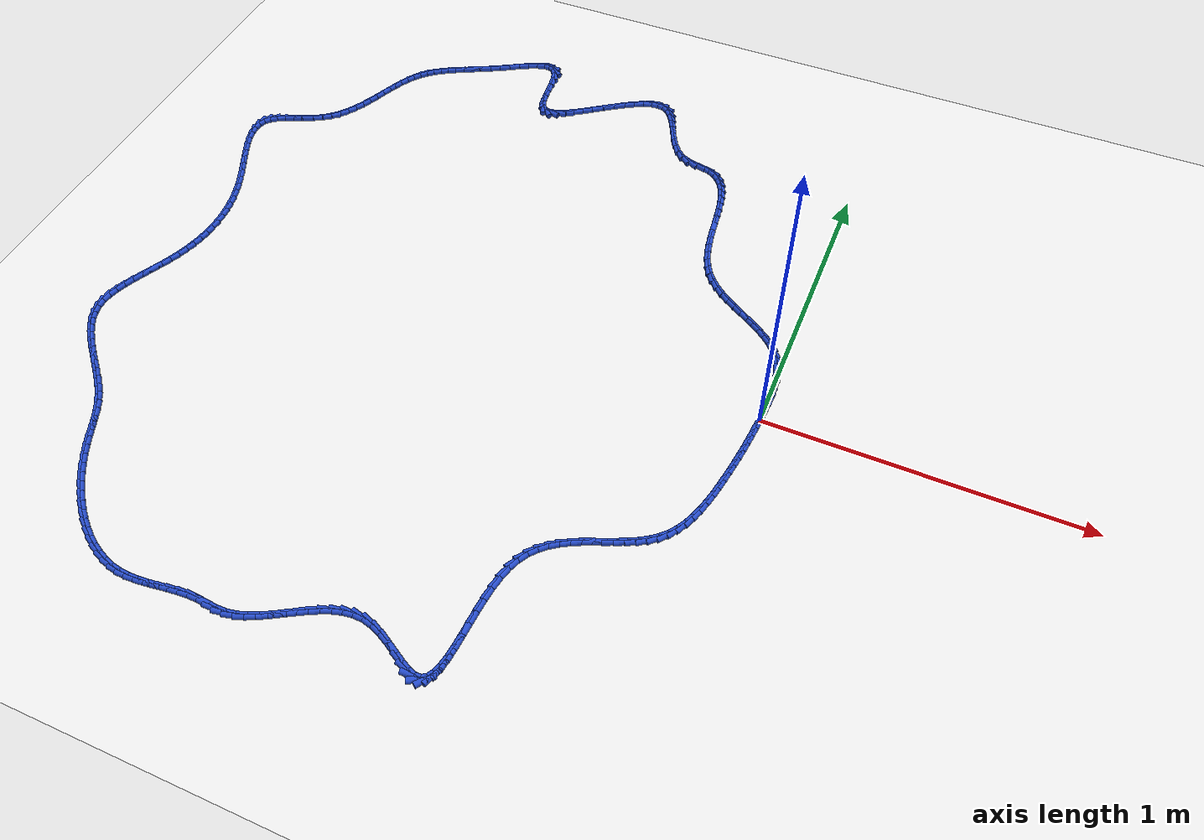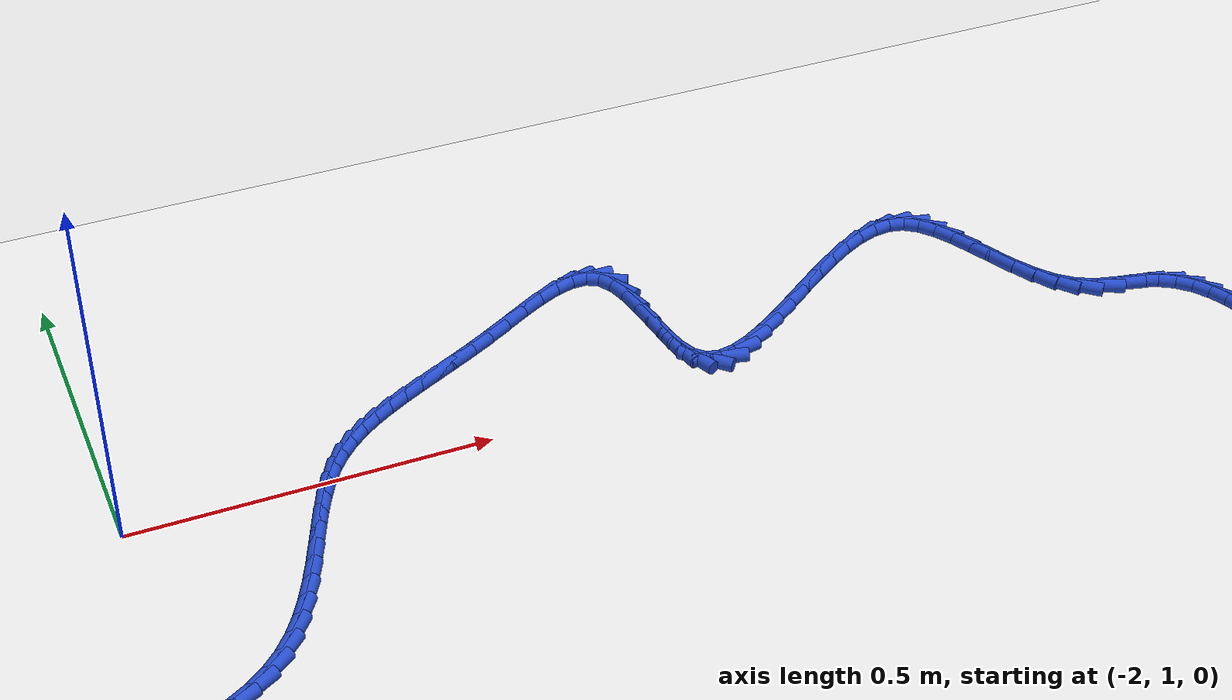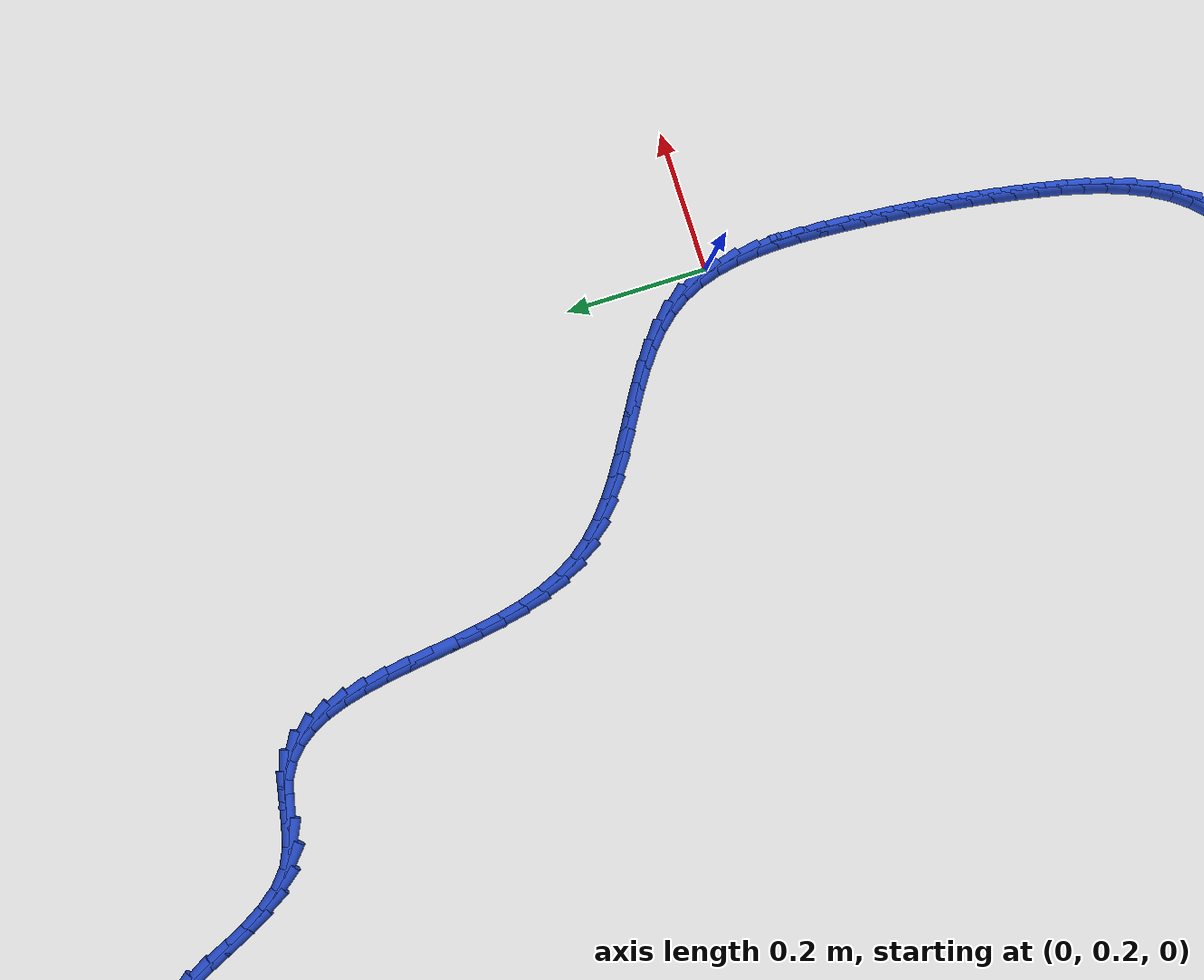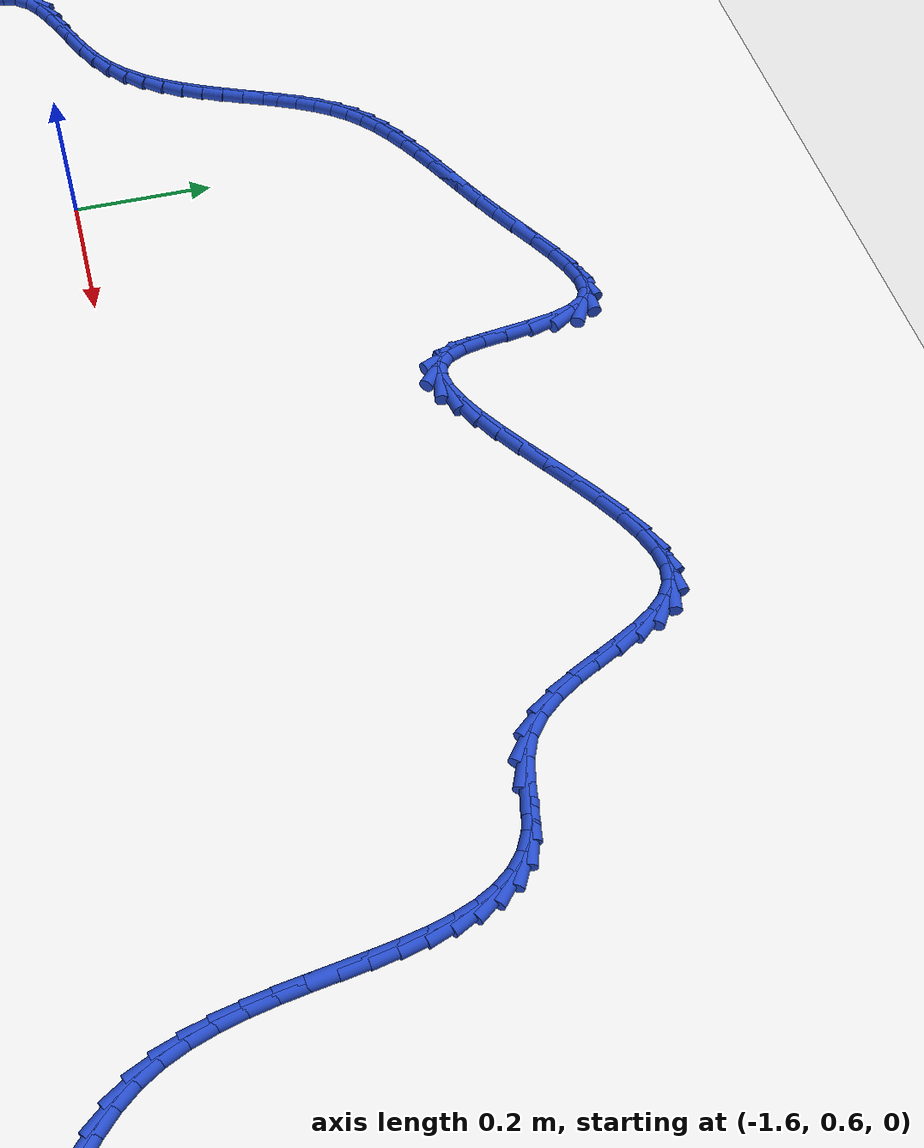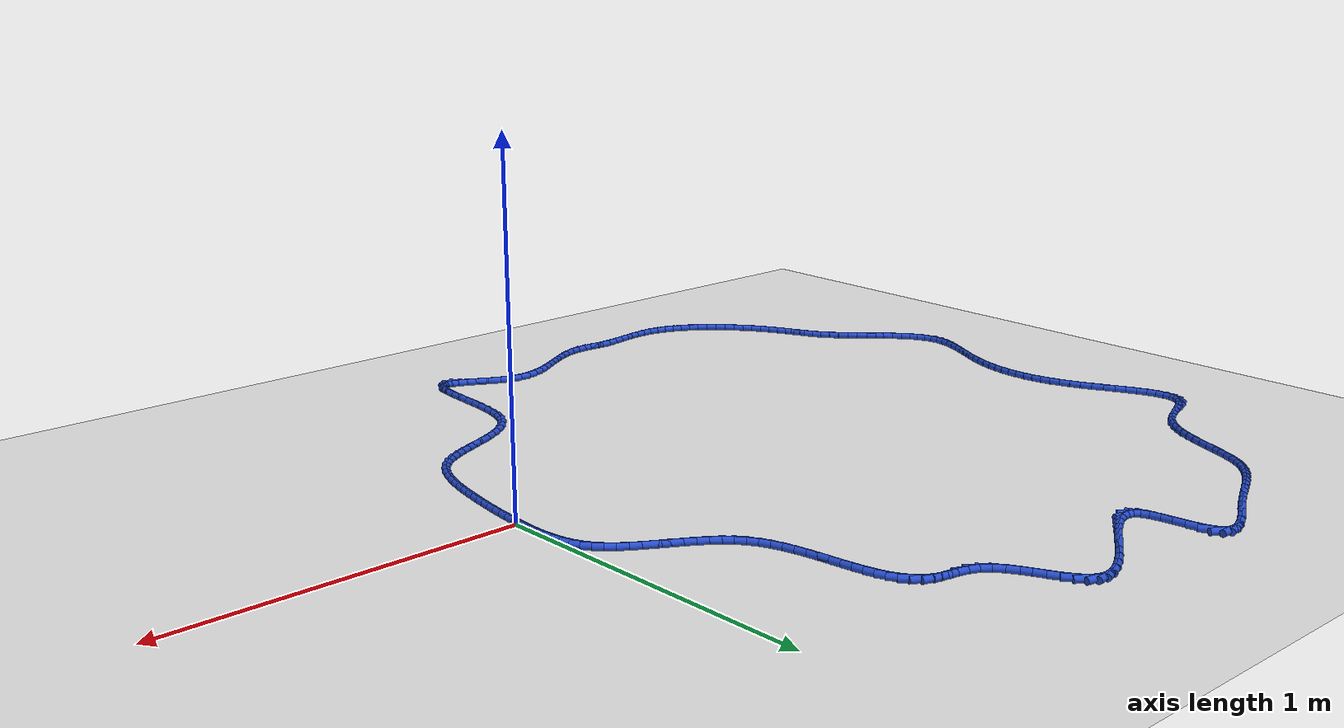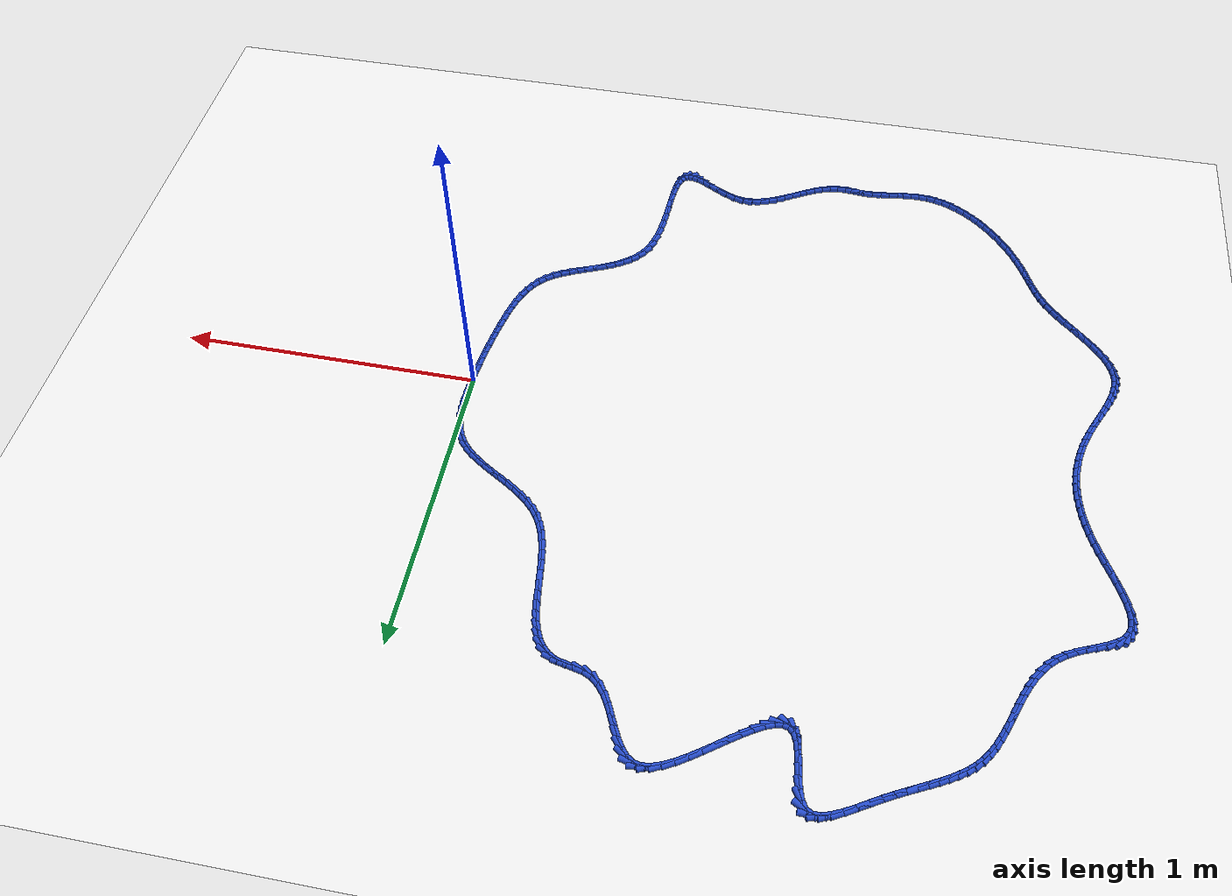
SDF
<sdf version="1.6">
 <world name="default">
  <light name="sun" type="directional">
   <pose>0 0 10 0 -0 0</pose>
   <diffuse>0.8 0.8 0.8 1</diffuse>
   <specular>0.2 0.2 0.2 1</specular>
   <attenuation>
    <range>1000</range>
    <constant>0.9</constant>
    <linear>0.01</linear>
    <quadratic>0.001</quadratic>
   </attenuation>
   <direction>-0.5 0.1 -0.9</direction>
  </light>
  <model name="ground_plane">
   <static>1</static>
   <link name="link">
    <collision name="collision">
     <geometry><plane><normal>0 0 1</normal><size>100 100</size></plane></geometry>
     <surface><friction><ode><mu>100</mu><mu2>50</mu2></ode></friction></surface>
    </collision>
    <visual name="visual">
     <cast_shadows>0</cast_shadows>
     <geometry><plane><normal>0 0 1</normal><size>100 100</size></plane></geometry>
     <material>
      <script><uri>file://media/materials/scripts/gazebo.material</uri><name>Gazebo/WhiteGlow</name></script>
     </material>
    </visual>
   </link>
  </model>
  <gravity>0 0 -9.8</gravity>
  <magnetic_field>6e-06 2.3e-05 -4.2e-05</magnetic_field>
  <atmosphere type="adiabatic"/>
  <physics name="default_physics" default="0" type="ode">
   <max_step_size>0.001</max_step_size>
   <real_time_factor>1</real_time_factor>
   <real_time_update_rate>1000</real_time_update_rate>
  </physics>
  <scene><ambient>0.4 0.4 0.4 1</ambient><background>0.7 0.7 0.7 1</background><shadows>1</shadows></scene>
  <spherical_coordinates>
   <surface_model>EARTH_WGS84</surface_model>
   <latitude_deg>0</latitude_deg>
   <longitude_deg>0</longitude_deg>
   <elevation>0</elevation>
   <heading_deg>0</heading_deg>
  </spherical_coordinates>
  <model name="line">
   <link name="link_0">
    <pose>-3.903127820947816e-18 -1.3877787807814457e-16 0.01 0 1.57 1.5075836220869705</pose>
    <collision name="collision">
     <geometry><cylinder><radius>0.01</radius><length>0.08</length></cylinder></geometry>
    </collision>
    <visual name="visual">
     <material>
      <script><name>Gazebo/Blue</name><uri>file://media/materials/scripts/gazebo.material</uri></script>
     </material>
     <geometry><cylinder><radius>0.01</radius><length>0.08</length></cylinder></geometry>
    </visual>
   </link>
   <link name="link_1">
    <pose>0.0020164505479032184 0.03185695079526101 0.01 0 1.57 1.5313063499105368</pose>
    <collision name="collision">
     <geometry><cylinder><radius>0.01</radius><length>0.08</length></cylinder></geometry>
    </collision>
    <visual name="visual">
     <material>
      <script><name>Gazebo/Blue</name><uri>file://media/materials/scripts/gazebo.material</uri></script>
     </material>
     <geometry><cylinder><radius>0.01</radius><length>0.08</length></cylinder></geometry>
    </visual>
   </link>
   <link name="link_2">
    <pose>0.0032904388714438586 0.06410123431389136 0.01 0 1.57 1.5672807837218443</pose>
    <collision name="collision">
     <geometry><cylinder><radius>0.01</radius><length>0.08</length></cylinder></geometry>
    </collision>
    <visual name="visual">
     <material>
      <script><name>Gazebo/Blue</name><uri>file://media/materials/scripts/gazebo.material</uri></script>
     </material>
     <geometry><cylinder><radius>0.01</radius><length>0.08</length></cylinder></geometry>
    </visual>
   </link>
   <link name="link_3">
    <pose>0.003403725928168772 0.096325726423337 0.01 0 1.57 -1.5247356906483298</pose>
    <collision name="collision">
     <geometry><cylinder><radius>0.01</radius><length>0.08</length></cylinder></geometry>
    </collision>
    <visual name="visual">
     <material>
      <script><name>Gazebo/Blue</name><uri>file://media/materials/scripts/gazebo.material</uri></script>
     </material>
     <geometry><cylinder><radius>0.01</radius><length>0.08</length></cylinder></geometry>
    </visual>
   </link>
   <link name="link_4">
    <pose>0.0019380726756248095 0.12812330299104396 0.01 0 1.57 -1.4594232896090267</pose>
    <collision name="collision">
     <geometry><cylinder><radius>0.01</radius><length>0.08</length></cylinder></geometry>
    </collision>
    <visual name="visual">
     <material>
      <script><name>Gazebo/Blue</name><uri>file://media/materials/scripts/gazebo.material</uri></script>
     </material>
     <geometry><cylinder><radius>0.01</radius><length>0.08</length></cylinder></geometry>
    </visual>
   </link>
   <link name="link_5">
    <pose>-0.0015247599286411775 0.15908683988445826 0.01 0 1.57 -1.375544059959423</pose>
    <collision name="collision">
     <geometry><cylinder><radius>0.01</radius><length>0.08</length></cylinder></geometry>
    </collision>
    <visual name="visual">
     <material>
      <script><name>Gazebo/Blue</name><uri>file://media/materials/scripts/gazebo.material</uri></script>
     </material>
     <geometry><cylinder><radius>0.01</radius><length>0.08</length></cylinder></geometry>
    </visual>
   </link>
   <link name="link_6">
    <pose>-0.007403010927082336 0.18880921297102593 0.01 0 1.57 -1.2699000928512538</pose>
    <collision name="collision">
     <geometry><cylinder><radius>0.01</radius><length>0.08</length></cylinder></geometry>
    </collision>
    <visual name="visual">
     <material>
      <script><name>Gazebo/Blue</name><uri>file://media/materials/scripts/gazebo.material</uri></script>
     </material>
     <geometry><cylinder><radius>0.01</radius><length>0.08</length></cylinder></geometry>
    </visual>
   </link>
   <link name="link_7">
    <pose>-0.016114919362151814 0.21688329811819312 0.01 0 1.57 -1.1398093752033278</pose>
    <collision name="collision">
     <geometry><cylinder><radius>0.01</radius><length>0.08</length></cylinder></geometry>
    </collision>
    <visual name="visual">
     <material>
      <script><name>Gazebo/Blue</name><uri>file://media/materials/scripts/gazebo.material</uri></script>
     </material>
     <geometry><cylinder><radius>0.01</radius><length>0.08</length></cylinder></geometry>
    </visual>
   </link>
   <link name="link_8">
    <pose>-0.02807872427630276 0.24290197119340579 0.01 0 1.57 -0.9881987893661152</pose>
    <collision name="collision">
     <geometry><cylinder><radius>0.01</radius><length>0.08</length></cylinder></geometry>
    </collision>
    <visual name="visual">
     <material>
      <script><name>Gazebo/Blue</name><uri>file://media/materials/scripts/gazebo.material</uri></script>
     </material>
     <geometry><cylinder><radius>0.01</radius><length>0.08</length></cylinder></geometry>
    </visual>
   </link>
   <link name="link_9">
    <pose>-0.04364009713171598 0.26651962588731637 0.01 0 1.57 -0.846864442697634</pose>
    <collision name="collision">
     <geometry><cylinder><radius>0.01</radius><length>0.08</length></cylinder></geometry>
    </collision>
    <visual name="visual">
     <material>
      <script><name>Gazebo/Blue</name><uri>file://media/materials/scripts/gazebo.material</uri></script>
     </material>
     <geometry><cylinder><radius>0.01</radius><length>0.08</length></cylinder></geometry>
    </visual>
   </link>
   <link name="link_10">
    <pose>-0.06254245248338933 0.2879012080379926 0.01 0 1.57 -0.7339181928377716</pose>
    <collision name="collision">
     <geometry><cylinder><radius>0.01</radius><length>0.08</length></cylinder></geometry>
    </collision>
    <visual name="visual">
     <material>
      <script><name>Gazebo/Blue</name><uri>file://media/materials/scripts/gazebo.material</uri></script>
     </material>
     <geometry><cylinder><radius>0.01</radius><length>0.08</length></cylinder></geometry>
    </visual>
   </link>
   <link name="link_11">
    <pose>-0.08423112233999577 0.3074643574456941 0.01 0 1.57 -0.6495082023152806</pose>
    <collision name="collision">
     <geometry><cylinder><radius>0.01</radius><length>0.08</length></cylinder></geometry>
    </collision>
    <visual name="visual">
     <material>
      <script><name>Gazebo/Blue</name><uri>file://media/materials/scripts/gazebo.material</uri></script>
     </material>
     <geometry><cylinder><radius>0.01</radius><length>0.08</length></cylinder></geometry>
    </visual>
   </link>
   <link name="link_12">
    <pose>-0.10814931214468339 0.32562851666724923 0.01 0 1.57 -0.591349700956301</pose>
    <collision name="collision">
     <geometry><cylinder><radius>0.01</radius><length>0.08</length></cylinder></geometry>
    </collision>
    <visual name="visual">
     <material>
      <script><name>Gazebo/Blue</name><uri>file://media/materials/scripts/gazebo.material</uri></script>
     </material>
     <geometry><cylinder><radius>0.01</radius><length>0.08</length></cylinder></geometry>
    </visual>
   </link>
   <link name="link_13">
    <pose>-0.1337402273406002 0.3428131282594858 0.01 0 1.57 -0.5567859104704407</pose>
    <collision name="collision">
     <geometry><cylinder><radius>0.01</radius><length>0.08</length></cylinder></geometry>
    </collision>
    <visual name="visual">
     <material>
      <script><name>Gazebo/Blue</name><uri>file://media/materials/scripts/gazebo.material</uri></script>
     </material>
     <geometry><cylinder><radius>0.01</radius><length>0.08</length></cylinder></geometry>
    </visual>
   </link>
   <link name="link_14">
    <pose>-0.1604470733708942 0.3594376347792322 0.01 0 1.57 -0.5437635951876674</pose>
    <collision name="collision">
     <geometry><cylinder><radius>0.01</radius><length>0.08</length></cylinder></geometry>
    </collision>
    <visual name="visual">
     <material>
      <script><name>Gazebo/Blue</name><uri>file://media/materials/scripts/gazebo.material</uri></script>
     </material>
     <geometry><cylinder><radius>0.01</radius><length>0.08</length></cylinder></geometry>
    </visual>
   </link>
   <link name="link_15">
    <pose>-0.1877130556787135 0.3759214787833164 0.01 0 1.57 -0.5511791643567712</pose>
    <collision name="collision">
     <geometry><cylinder><radius>0.01</radius><length>0.08</length></cylinder></geometry>
    </collision>
    <visual name="visual">
     <material>
      <script><name>Gazebo/Blue</name><uri>file://media/materials/scripts/gazebo.material</uri></script>
     </material>
     <geometry><cylinder><radius>0.01</radius><length>0.08</length></cylinder></geometry>
    </visual>
   </link>
   <link name="link_16">
    <pose>-0.21498137970720602 0.3926841028285664 0.01 0 1.57 -0.5789191369160495</pose>
    <collision name="collision">
     <geometry><cylinder><radius>0.01</radius><length>0.08</length></cylinder></geometry>
    </collision>
    <visual name="visual">
     <material>
      <script><name>Gazebo/Blue</name><uri>file://media/materials/scripts/gazebo.material</uri></script>
     </material>
     <geometry><cylinder><radius>0.01</radius><length>0.08</length></cylinder></geometry>
    </visual>
   </link>
   <link name="link_17">
    <pose>-0.24169525089951993 0.41014494947181074 0.01 0 1.57 -0.627733292693414</pose>
    <collision name="collision">
     <geometry><cylinder><radius>0.01</radius><length>0.08</length></cylinder></geometry>
    </collision>
    <visual name="visual">
     <material>
      <script><name>Gazebo/Blue</name><uri>file://media/materials/scripts/gazebo.material</uri></script>
     </material>
     <geometry><cylinder><radius>0.01</radius><length>0.08</length></cylinder></geometry>
    </visual>
   </link>
   <link name="link_18">
    <pose>-0.26729787469880323 0.4287234612698771 0.01 0 1.57 -0.6989187107194657</pose>
    <collision name="collision">
     <geometry><cylinder><radius>0.01</radius><length>0.08</length></cylinder></geometry>
    </collision>
    <visual name="visual">
     <material>
      <script><name>Gazebo/Blue</name><uri>file://media/materials/scripts/gazebo.material</uri></script>
     </material>
     <geometry><cylinder><radius>0.01</radius><length>0.08</length></cylinder></geometry>
    </visual>
   </link>
   <link name="link_19">
    <pose>-0.2912324565482039 0.4488390807795937 0.01 0 1.57 -0.7936759227544717</pose>
    <collision name="collision">
     <geometry><cylinder><radius>0.01</radius><length>0.08</length></cylinder></geometry>
    </collision>
    <visual name="visual">
     <material>
      <script><name>Gazebo/Blue</name><uri>file://media/materials/scripts/gazebo.material</uri></script>
     </material>
     <geometry><cylinder><radius>0.01</radius><length>0.08</length></cylinder></geometry>
    </visual>
   </link>
   <link name="link_20">
    <pose>-0.31294220189086996 0.4709112505577889 0.01 0 1.57 -0.9119773880350294</pose>
    <collision name="collision">
     <geometry><cylinder><radius>0.01</radius><length>0.08</length></cylinder></geometry>
    </collision>
    <visual name="visual">
     <material>
      <script><name>Gazebo/Blue</name><uri>file://media/materials/scripts/gazebo.material</uri></script>
     </material>
     <geometry><cylinder><radius>0.01</radius><length>0.08</length></cylinder></geometry>
    </visual>
   </link>
   <link name="link_21">
    <pose>-0.33187031616994955 0.4953594131612905 0.01 0 1.57 -1.0485901152458557</pose>
    <collision name="collision">
     <geometry><cylinder><radius>0.01</radius><length>0.08</length></cylinder></geometry>
    </collision>
    <visual name="visual">
     <material>
      <script><name>Gazebo/Blue</name><uri>file://media/materials/scripts/gazebo.material</uri></script>
     </material>
     <geometry><cylinder><radius>0.01</radius><length>0.08</length></cylinder></geometry>
    </visual>
   </link>
   <link name="link_22">
    <pose>-0.3475195333807346 0.5225520334368505 0.01 0 1.57 -1.1731074590070527</pose>
    <collision name="collision">
     <geometry><cylinder><radius>0.01</radius><length>0.08</length></cylinder></geometry>
    </collision>
    <visual name="visual">
     <material>
      <script><name>Gazebo/Blue</name><uri>file://media/materials/scripts/gazebo.material</uri></script>
     </material>
     <geometry><cylinder><radius>0.01</radius><length>0.08</length></cylinder></geometry>
    </visual>
   </link>
   <link name="link_23">
    <pose>-0.3600231857537802 0.5523175588302576 0.01 0 1.57 -1.2701942811796618</pose>
    <collision name="collision">
     <geometry><cylinder><radius>0.01</radius><length>0.08</length></cylinder></geometry>
    </collision>
    <visual name="visual">
     <material>
      <script><name>Gazebo/Blue</name><uri>file://media/materials/scripts/gazebo.material</uri></script>
     </material>
     <geometry><cylinder><radius>0.01</radius><length>0.08</length></cylinder></geometry>
    </visual>
   </link>
   <link name="link_24">
    <pose>-0.3698940579065953 0.5841594899664346 0.01 0 1.57 -1.3427371461727866</pose>
    <collision name="collision">
     <geometry><cylinder><radius>0.01</radius><length>0.08</length></cylinder></geometry>
    </collision>
    <visual name="visual">
     <material>
      <script><name>Gazebo/Blue</name><uri>file://media/materials/scripts/gazebo.material</uri></script>
     </material>
     <geometry><cylinder><radius>0.01</radius><length>0.08</length></cylinder></geometry>
    </visual>
   </link>
   <link name="link_25">
    <pose>-0.3776501348054274 0.6175768741137091 0.01 0 1.57 -1.3940874275996893</pose>
    <collision name="collision">
     <geometry><cylinder><radius>0.01</radius><length>0.08</length></cylinder></geometry>
    </collision>
    <visual name="visual">
     <material>
      <script><name>Gazebo/Blue</name><uri>file://media/materials/scripts/gazebo.material</uri></script>
     </material>
     <geometry><cylinder><radius>0.01</radius><length>0.08</length></cylinder></geometry>
    </visual>
   </link>
   <link name="link_26">
    <pose>-0.38380940141652425 0.6520687585404089 0.01 0 1.57 -1.4269129249123744</pose>
    <collision name="collision">
     <geometry><cylinder><radius>0.01</radius><length>0.08</length></cylinder></geometry>
    </collision>
    <visual name="visual">
     <material>
      <script><name>Gazebo/Blue</name><uri>file://media/materials/scripts/gazebo.material</uri></script>
     </material>
     <geometry><cylinder><radius>0.01</radius><length>0.08</length></cylinder></geometry>
    </visual>
   </link>
   <link name="link_27">
    <pose>-0.38888984270613347 0.6871341905148619 0.01 0 1.57 -1.442874485544371</pose>
    <collision name="collision">
     <geometry><cylinder><radius>0.01</radius><length>0.08</length></cylinder></geometry>
    </collision>
    <visual name="visual">
     <material>
      <script><name>Gazebo/Blue</name><uri>file://media/materials/scripts/gazebo.material</uri></script>
     </material>
     <geometry><cylinder><radius>0.01</radius><length>0.08</length></cylinder></geometry>
    </visual>
   </link>
   <link name="link_28">
    <pose>-0.3934094436405026 0.722272217305396 0.01 0 1.57 -1.4425275494494239</pose>
    <collision name="collision">
     <geometry><cylinder><radius>0.01</radius><length>0.08</length></cylinder></geometry>
    </collision>
    <visual name="visual">
     <material>
      <script><name>Gazebo/Blue</name><uri>file://media/materials/scripts/gazebo.material</uri></script>
     </material>
     <geometry><cylinder><radius>0.01</radius><length>0.08</length></cylinder></geometry>
    </visual>
   </link>
   <link name="link_29">
    <pose>-0.3978861891858792 0.7569818861803387 0.01 0 1.57 -1.4252426396143179</pose>
    <collision name="collision">
     <geometry><cylinder><radius>0.01</radius><length>0.08</length></cylinder></geometry>
    </collision>
    <visual name="visual">
     <material>
      <script><name>Gazebo/Blue</name><uri>file://media/materials/scripts/gazebo.material</uri></script>
     </material>
     <geometry><cylinder><radius>0.01</radius><length>0.08</length></cylinder></geometry>
    </visual>
   </link>
   <link name="link_30">
    <pose>-0.402838064308511 0.7907622444080178 0.01 0 1.57 -1.3890537372332847</pose>
    <collision name="collision">
     <geometry><cylinder><radius>0.01</radius><length>0.08</length></cylinder></geometry>
    </collision>
    <visual name="visual">
     <material>
      <script><name>Gazebo/Blue</name><uri>file://media/materials/scripts/gazebo.material</uri></script>
     </material>
     <geometry><cylinder><radius>0.01</radius><length>0.08</length></cylinder></geometry>
    </visual>
   </link>
   <link name="link_31">
    <pose>-0.4087830539746455 0.8231123392567612 0.01 0 1.57 -1.3304216321388194</pose>
    <collision name="collision">
     <geometry><cylinder><radius>0.01</radius><length>0.08</length></cylinder></geometry>
    </collision>
    <visual name="visual">
     <material>
      <script><name>Gazebo/Blue</name><uri>file://media/materials/scripts/gazebo.material</uri></script>
     </material>
     <geometry><cylinder><radius>0.01</radius><length>0.08</length></cylinder></geometry>
    </visual>
   </link>
   <link name="link_32">
    <pose>-0.41623914315053046 0.853531217994897 0.01 0 1.57 -1.2440288575850311</pose>
    <collision name="collision">
     <geometry><cylinder><radius>0.01</radius><length>0.08</length></cylinder></geometry>
    </collision>
    <visual name="visual">
     <material>
      <script><name>Gazebo/Blue</name><uri>file://media/materials/scripts/gazebo.material</uri></script>
     </material>
     <geometry><cylinder><radius>0.01</radius><length>0.08</length></cylinder></geometry>
    </visual>
   </link>
   <link name="link_33">
    <pose>-0.42572431680241307 0.881517927890752 0.01 0 1.57 -1.1230648402112118</pose>
    <collision name="collision">
     <geometry><cylinder><radius>0.01</radius><length>0.08</length></cylinder></geometry>
    </collision>
    <visual name="visual">
     <material>
      <script><name>Gazebo/Blue</name><uri>file://media/materials/scripts/gazebo.material</uri></script>
     </material>
     <geometry><cylinder><radius>0.01</radius><length>0.08</length></cylinder></geometry>
    </visual>
   </link>
   <link name="link_34">
    <pose>-0.4377565598965416 0.9065715162126552 0.01 0 1.57 -0.9612000604306511</pose>
    <collision name="collision">
     <geometry><cylinder><radius>0.01</radius><length>0.08</length></cylinder></geometry>
    </collision>
    <visual name="visual">
     <material>
      <script><name>Gazebo/Blue</name><uri>file://media/materials/scripts/gazebo.material</uri></script>
     </material>
     <geometry><cylinder><radius>0.01</radius><length>0.08</length></cylinder></geometry>
    </visual>
   </link>
   <link name="link_35">
    <pose>-0.45285385739916295 0.9281910302289332 0.01 0 1.57 -0.7580200280680599</pose>
    <collision name="collision">
     <geometry><cylinder><radius>0.01</radius><length>0.08</length></cylinder></geometry>
    </collision>
    <visual name="visual">
     <material>
      <script><name>Gazebo/Blue</name><uri>file://media/materials/scripts/gazebo.material</uri></script>
     </material>
     <geometry><cylinder><radius>0.01</radius><length>0.08</length></cylinder></geometry>
    </visual>
   </link>
   <link name="link_36">
    <pose>-0.4715341942765252 0.9458755172079145 0.01 0 1.57 -0.5267430619988737</pose>
    <collision name="collision">
     <geometry><cylinder><radius>0.01</radius><length>0.08</length></cylinder></geometry>
    </collision>
    <visual name="visual">
     <material>
      <script><name>Gazebo/Blue</name><uri>file://media/materials/scripts/gazebo.material</uri></script>
     </material>
     <geometry><cylinder><radius>0.01</radius><length>0.08</length></cylinder></geometry>
    </visual>
   </link>
   <link name="link_37">
    <pose>-0.4943155554948757 0.9591240244179267 0.01 0 1.57 -0.30266845434637196</pose>
    <collision name="collision">
     <geometry><cylinder><radius>0.01</radius><length>0.08</length></cylinder></geometry>
    </collision>
    <visual name="visual">
     <material>
      <script><name>Gazebo/Blue</name><uri>file://media/materials/scripts/gazebo.material</uri></script>
     </material>
     <geometry><cylinder><radius>0.01</radius><length>0.08</length></cylinder></geometry>
    </visual>
   </link>
   <link name="link_38">
    <pose>-0.5215664681722004 0.9676334616616956 0.01 0 1.57 -0.19589830308612133</pose>
    <collision name="collision">
     <geometry><cylinder><radius>0.01</radius><length>0.08</length></cylinder></geometry>
    </collision>
    <visual name="visual">
     <material>
      <script><name>Gazebo/Blue</name><uri>file://media/materials/scripts/gazebo.material</uri></script>
     </material>
     <geometry><cylinder><radius>0.01</radius><length>0.08</length></cylinder></geometry>
    </visual>
   </link>
   <link name="link_39">
    <pose>-0.5517500883862227 0.9736231994047991 0.01 0 1.57 -0.2407019473134566</pose>
    <collision name="collision">
     <geometry><cylinder><radius>0.01</radius><length>0.08</length></cylinder></geometry>
    </collision>
    <visual name="visual">
     <material>
      <script><name>Gazebo/Blue</name><uri>file://media/materials/scripts/gazebo.material</uri></script>
     </material>
     <geometry><cylinder><radius>0.01</radius><length>0.08</length></cylinder></geometry>
    </visual>
   </link>
   <link name="link_40">
    <pose>-0.5820155604673277 0.9810521868474292 0.01 0 1.57 -0.43623362921171305</pose>
    <collision name="collision">
     <geometry><cylinder><radius>0.01</radius><length>0.08</length></cylinder></geometry>
    </collision>
    <visual name="visual">
     <material>
      <script><name>Gazebo/Blue</name><uri>file://media/materials/scripts/gazebo.material</uri></script>
     </material>
     <geometry><cylinder><radius>0.01</radius><length>0.08</length></cylinder></geometry>
    </visual>
   </link>
   <link name="link_41">
    <pose>-0.6095134380599755 0.9938713542574893 0.01 0 1.57 -0.7072970957256787</pose>
    <collision name="collision">
     <geometry><cylinder><radius>0.01</radius><length>0.08</length></cylinder></geometry>
    </collision>
    <visual name="visual">
     <material>
      <script><name>Gazebo/Blue</name><uri>file://media/materials/scripts/gazebo.material</uri></script>
     </material>
     <geometry><cylinder><radius>0.01</radius><length>0.08</length></cylinder></geometry>
    </visual>
   </link>
   <link name="link_42">
    <pose>-0.6328324273686436 1.0138053536102383 0.01 0 1.57 -0.9093988808996616</pose>
    <collision name="collision">
     <geometry><cylinder><radius>0.01</radius><length>0.08</length></cylinder></geometry>
    </collision>
    <visual name="visual">
     <material>
      <script><name>Gazebo/Blue</name><uri>file://media/materials/scripts/gazebo.material</uri></script>
     </material>
     <geometry><cylinder><radius>0.01</radius><length>0.08</length></cylinder></geometry>
    </visual>
   </link>
   <link name="link_43">
    <pose>-0.652677863115749 1.039302269252374 0.01 0 1.57 -1.0379672441169334</pose>
    <collision name="collision">
     <geometry><cylinder><radius>0.01</radius><length>0.08</length></cylinder></geometry>
    </collision>
    <visual name="visual">
     <material>
      <script><name>Gazebo/Blue</name><uri>file://media/materials/scripts/gazebo.material</uri></script>
     </material>
     <geometry><cylinder><radius>0.01</radius><length>0.08</length></cylinder></geometry>
    </visual>
   </link>
   <link name="link_44">
    <pose>-0.6699246125816707 1.0685477469936964 0.01 0 1.57 -1.108867010465671</pose>
    <collision name="collision">
     <geometry><cylinder><radius>0.01</radius><length>0.08</length></cylinder></geometry>
    </collision>
    <visual name="visual">
     <material>
      <script><name>Gazebo/Blue</name><uri>file://media/materials/scripts/gazebo.material</uri></script>
     </material>
     <geometry><cylinder><radius>0.01</radius><length>0.08</length></cylinder></geometry>
    </visual>
   </link>
   <link name="link_45">
    <pose>-0.6854475430467871 1.0997274326440063 0.01 0 1.57 -1.1323990076663486</pose>
    <collision name="collision">
     <geometry><cylinder><radius>0.01</radius><length>0.08</length></cylinder></geometry>
    </collision>
    <visual name="visual">
     <material>
      <script><name>Gazebo/Blue</name><uri>file://media/materials/scripts/gazebo.material</uri></script>
     </material>
     <geometry><cylinder><radius>0.01</radius><length>0.08</length></cylinder></geometry>
    </visual>
   </link>
   <link name="link_46">
    <pose>-0.7001215217914767 1.1310269720131048 0.01 0 1.57 -1.109925741718624</pose>
    <collision name="collision">
     <geometry><cylinder><radius>0.01</radius><length>0.08</length></cylinder></geometry>
    </collision>
    <visual name="visual">
     <material>
      <script><name>Gazebo/Blue</name><uri>file://media/materials/scripts/gazebo.material</uri></script>
     </material>
     <geometry><cylinder><radius>0.01</radius><length>0.08</length></cylinder></geometry>
    </visual>
   </link>
   <link name="link_47">
    <pose>-0.7148214160961184 1.1606320109107924 0.01 0 1.57 -1.0319853666192091</pose>
    <collision name="collision">
     <geometry><cylinder><radius>0.01</radius><length>0.08</length></cylinder></geometry>
    </collision>
    <visual name="visual">
     <material>
      <script><name>Gazebo/Blue</name><uri>file://media/materials/scripts/gazebo.material</uri></script>
     </material>
     <geometry><cylinder><radius>0.01</radius><length>0.08</length></cylinder></geometry>
    </visual>
   </link>
   <link name="link_48">
    <pose>-0.7304220932410903 1.1867281951468691 0.01 0 1.57 -0.8741996581504637</pose>
    <collision name="collision">
     <geometry><cylinder><radius>0.01</radius><length>0.08</length></cylinder></geometry>
    </collision>
    <visual name="visual">
     <material>
      <script><name>Gazebo/Blue</name><uri>file://media/materials/scripts/gazebo.material</uri></script>
     </material>
     <geometry><cylinder><radius>0.01</radius><length>0.08</length></cylinder></geometry>
    </visual>
   </link>
   <link name="link_49">
    <pose>-0.7477984205067714 1.2075011705311365 0.01 0 1.57 -0.5977622757171739</pose>
    <collision name="collision">
     <geometry><cylinder><radius>0.01</radius><length>0.08</length></cylinder></geometry>
    </collision>
    <visual name="visual">
     <material>
      <script><name>Gazebo/Blue</name><uri>file://media/materials/scripts/gazebo.material</uri></script>
     </material>
     <geometry><cylinder><radius>0.01</radius><length>0.08</length></cylinder></geometry>
    </visual>
   </link>
   <link name="link_50">
    <pose>-0.7678252651735397 1.221136582873394 0.01 0 1.57 -0.20885263576957408</pose>
    <collision name="collision">
     <geometry><cylinder><radius>0.01</radius><length>0.08</length></cylinder></geometry>
    </collision>
    <visual name="visual">
     <material>
      <script><name>Gazebo/Blue</name><uri>file://media/materials/scripts/gazebo.material</uri></script>
     </material>
     <geometry><cylinder><radius>0.01</radius><length>0.08</length></cylinder></geometry>
    </visual>
   </link>
   <link name="link_51">
    <pose>-0.7912476072692822 1.226100790144109 0.01 0 1.57 0.12068090379388059</pose>
    <collision name="collision">
     <geometry><cylinder><radius>0.01</radius><length>0.08</length></cylinder></geometry>
    </collision>
    <visual name="visual">
     <material>
      <script><name>Gazebo/Blue</name><uri>file://media/materials/scripts/gazebo.material</uri></script>
     </material>
     <geometry><cylinder><radius>0.01</radius><length>0.08</length></cylinder></geometry>
    </visual>
   </link>
   <link name="link_52">
    <pose>-0.8178799573203202 1.2228710797868647 0.01 0 1.57 0.3315336128403359</pose>
    <collision name="collision">
     <geometry><cylinder><radius>0.01</radius><length>0.08</length></cylinder></geometry>
    </collision>
    <visual name="visual">
     <material>
      <script><name>Gazebo/Blue</name><uri>file://media/materials/scripts/gazebo.material</uri></script>
     </material>
     <geometry><cylinder><radius>0.01</radius><length>0.08</length></cylinder></geometry>
    </visual>
   </link>
   <link name="link_53">
    <pose>-0.8471310487269955 1.2128017042406312 0.01 0 1.57 0.4614123259922743</pose>
    <collision name="collision">
     <geometry><cylinder><radius>0.01</radius><length>0.08</length></cylinder></geometry>
    </collision>
    <visual name="visual">
     <material>
      <script><name>Gazebo/Blue</name><uri>file://media/materials/scripts/gazebo.material</uri></script>
     </material>
     <geometry><cylinder><radius>0.01</radius><length>0.08</length></cylinder></geometry>
    </visual>
   </link>
   <link name="link_54">
    <pose>-0.8784079301726923 1.1972505569524734 0.01 0 1.57 0.5415246053904844</pose>
    <collision name="collision">
     <geometry><cylinder><radius>0.01</radius><length>0.08</length></cylinder></geometry>
    </collision>
    <visual name="visual">
     <material>
      <script><name>Gazebo/Blue</name><uri>file://media/materials/scripts/gazebo.material</uri></script>
     </material>
     <geometry><cylinder><radius>0.01</radius><length>0.08</length></cylinder></geometry>
    </visual>
   </link>
   <link name="link_55">
    <pose>-0.9111176503407926 1.1775755313694554 0.01 0 1.57 0.5895405316093695</pose>
    <collision name="collision">
     <geometry><cylinder><radius>0.01</radius><length>0.08</length></cylinder></geometry>
    </collision>
    <visual name="visual">
     <material>
      <script><name>Gazebo/Blue</name><uri>file://media/materials/scripts/gazebo.material</uri></script>
     </material>
     <geometry><cylinder><radius>0.01</radius><length>0.08</length></cylinder></geometry>
    </visual>
   </link>
   <link name="link_56">
    <pose>-0.9446672579146804 1.1551345209386426 0.01 0 1.57 0.6145191289430184</pose>
    <collision name="collision">
     <geometry><cylinder><radius>0.01</radius><length>0.08</length></cylinder></geometry>
    </collision>
    <visual name="visual">
     <material>
      <script><name>Gazebo/Blue</name><uri>file://media/materials/scripts/gazebo.material</uri></script>
     </material>
     <geometry><cylinder><radius>0.01</radius><length>0.08</length></cylinder></geometry>
    </visual>
   </link>
   <link name="link_57">
    <pose>-0.9784638015777384 1.1312854191070996 0.01 0 1.57 0.6203695377131488</pose>
    <collision name="collision">
     <geometry><cylinder><radius>0.01</radius><length>0.08</length></cylinder></geometry>
    </collision>
    <visual name="visual">
     <material>
      <script><name>Gazebo/Blue</name><uri>file://media/materials/scripts/gazebo.material</uri></script>
     </material>
     <geometry><cylinder><radius>0.01</radius><length>0.08</length></cylinder></geometry>
    </visual>
   </link>
   <link name="link_58">
    <pose>-1.0119143300133497 1.1073861193218912 0.01 0 1.57 0.6072808321794766</pose>
    <collision name="collision">
     <geometry><cylinder><radius>0.01</radius><length>0.08</length></cylinder></geometry>
    </collision>
    <visual name="visual">
     <material>
      <script><name>Gazebo/Blue</name><uri>file://media/materials/scripts/gazebo.material</uri></script>
     </material>
     <geometry><cylinder><radius>0.01</radius><length>0.08</length></cylinder></geometry>
    </visual>
   </link>
   <link name="link_59">
    <pose>-1.044425891904898 1.0847945150300824 0.01 0 1.57 0.5715779477260751</pose>
    <collision name="collision">
     <geometry><cylinder><radius>0.01</radius><length>0.08</length></cylinder></geometry>
    </collision>
    <visual name="visual">
     <material>
      <script><name>Gazebo/Blue</name><uri>file://media/materials/scripts/gazebo.material</uri></script>
     </material>
     <geometry><cylinder><radius>0.01</radius><length>0.08</length></cylinder></geometry>
    </visual>
   </link>
   <link name="link_60">
    <pose>-1.0754055359357662 1.0648684996787376 0.01 0 1.57 0.5037050667707982</pose>
    <collision name="collision">
     <geometry><cylinder><radius>0.01</radius><length>0.08</length></cylinder></geometry>
    </collision>
    <visual name="visual">
     <material>
      <script><name>Gazebo/Blue</name><uri>file://media/materials/scripts/gazebo.material</uri></script>
     </material>
     <geometry><cylinder><radius>0.01</radius><length>0.08</length></cylinder></geometry>
    </visual>
   </link>
   <link name="link_61">
    <pose>-1.1042603107893374 1.0489659667149216 0.01 0 1.57 0.38269370177632833</pose>
    <collision name="collision">
     <geometry><cylinder><radius>0.01</radius><length>0.08</length></cylinder></geometry>
    </collision>
    <visual name="visual">
     <material>
      <script><name>Gazebo/Blue</name><uri>file://media/materials/scripts/gazebo.material</uri></script>
     </material>
     <geometry><cylinder><radius>0.01</radius><length>0.08</length></cylinder></geometry>
    </visual>
   </link>
   <link name="link_62">
    <pose>-1.130397265148994 1.038444809585699 0.01 0 1.57 0.16419048218357898</pose>
    <collision name="collision">
     <geometry><cylinder><radius>0.01</radius><length>0.08</length></cylinder></geometry>
    </collision>
    <visual name="visual">
     <material>
      <script><name>Gazebo/Blue</name><uri>file://media/materials/scripts/gazebo.material</uri></script>
     </material>
     <geometry><cylinder><radius>0.01</radius><length>0.08</length></cylinder></geometry>
    </visual>
   </link>
   <link name="link_63">
    <pose>-1.1532234476981205 1.034662921738135 0.01 0 1.57 -0.22421597552221068</pose>
    <collision name="collision">
     <geometry><cylinder><radius>0.01</radius><length>0.08</length></cylinder></geometry>
    </collision>
    <visual name="visual">
     <material>
      <script><name>Gazebo/Blue</name><uri>file://media/materials/scripts/gazebo.material</uri></script>
     </material>
     <geometry><cylinder><radius>0.01</radius><length>0.08</length></cylinder></geometry>
    </visual>
   </link>
   <link name="link_64">
    <pose>-1.172145907120099 1.038978196619294 0.01 0 1.57 -0.76211372244683</pose>
    <collision name="collision">
     <geometry><cylinder><radius>0.01</radius><length>0.08</length></cylinder></geometry>
    </collision>
    <visual name="visual">
     <material>
      <script><name>Gazebo/Blue</name><uri>file://media/materials/scripts/gazebo.material</uri></script>
     </material>
     <geometry><cylinder><radius>0.01</radius><length>0.08</length></cylinder></geometry>
    </visual>
   </link>
   <link name="link_65">
    <pose>-1.1865720754225162 1.0527477252090103 0.01 0 1.57 -1.176701932565536</pose>
    <collision name="collision">
     <geometry><cylinder><radius>0.01</radius><length>0.08</length></cylinder></geometry>
    </collision>
    <visual name="visual">
     <material>
      <script><name>Gazebo/Blue</name><uri>file://media/materials/scripts/gazebo.material</uri></script>
     </material>
     <geometry><cylinder><radius>0.01</radius><length>0.08</length></cylinder></geometry>
    </visual>
   </link>
   <link name="link_66">
    <pose>-1.196382306854327 1.0763385629009252 0.01 0 1.57 -1.3641741149394202</pose>
    <collision name="collision">
     <geometry><cylinder><radius>0.01</radius><length>0.08</length></cylinder></geometry>
    </collision>
    <visual name="visual">
     <material>
      <script><name>Gazebo/Blue</name><uri>file://media/materials/scripts/gazebo.material</uri></script>
     </material>
     <geometry><cylinder><radius>0.01</radius><length>0.08</length></cylinder></geometry>
    </visual>
   </link>
   <link name="link_67">
    <pose>-1.2028511145712488 1.1071991733842588 0.01 0 1.57 -1.4386640644127144</pose>
    <collision name="collision">
     <geometry><cylinder><radius>0.01</radius><length>0.08</length></cylinder></geometry>
    </collision>
    <visual name="visual">
     <material>
      <script><name>Gazebo/Blue</name><uri>file://media/materials/scripts/gazebo.material</uri></script>
     </material>
     <geometry><cylinder><radius>0.01</radius><length>0.08</length></cylinder></geometry>
    </visual>
   </link>
   <link name="link_68">
    <pose>-1.2075086519510703 1.1422428522064645 0.01 0 1.57 -1.4502869412167136</pose>
    <collision name="collision">
     <geometry><cylinder><radius>0.01</radius><length>0.08</length></cylinder></geometry>
    </collision>
    <visual name="visual">
     <material>
      <script><name>Gazebo/Blue</name><uri>file://media/materials/scripts/gazebo.material</uri></script>
     </material>
     <geometry><cylinder><radius>0.01</radius><length>0.08</length></cylinder></geometry>
    </visual>
   </link>
   <link name="link_69">
    <pose>-1.2118850723715813 1.1783828949149986 0.01 0 1.57 -1.4075332361102582</pose>
    <collision name="collision">
     <geometry><cylinder><radius>0.01</radius><length>0.08</length></cylinder></geometry>
    </collision>
    <visual name="visual">
     <material>
      <script><name>Gazebo/Blue</name><uri>file://media/materials/scripts/gazebo.material</uri></script>
     </material>
     <geometry><cylinder><radius>0.01</radius><length>0.08</length></cylinder></geometry>
    </visual>
   </link>
   <link name="link_70">
    <pose>-1.217510529210571 1.2125325970573153 0.01 0 1.57 -1.2893774932133544</pose>
    <collision name="collision">
     <geometry><cylinder><radius>0.01</radius><length>0.08</length></cylinder></geometry>
    </collision>
    <visual name="visual">
     <material>
      <script><name>Gazebo/Blue</name><uri>file://media/materials/scripts/gazebo.material</uri></script>
     </material>
     <geometry><cylinder><radius>0.01</radius><length>0.08</length></cylinder></geometry>
    </visual>
   </link>
   <link name="link_71">
    <pose>-1.2259151758458275 1.2416052541808689 0.01 0 1.57 -1.0244672539413715</pose>
    <collision name="collision">
     <geometry><cylinder><radius>0.01</radius><length>0.08</length></cylinder></geometry>
    </collision>
    <visual name="visual">
     <material>
      <script><name>Gazebo/Blue</name><uri>file://media/materials/scripts/gazebo.material</uri></script>
     </material>
     <geometry><cylinder><radius>0.01</radius><length>0.08</length></cylinder></geometry>
    </visual>
   </link>
   <link name="link_72">
    <pose>-1.2386291656551405 1.2625141618331148 0.01 0 1.57 -0.5061247348028546</pose>
    <collision name="collision">
     <geometry><cylinder><radius>0.01</radius><length>0.08</length></cylinder></geometry>
    </collision>
    <visual name="visual">
     <material>
      <script><name>Gazebo/Blue</name><uri>file://media/materials/scripts/gazebo.material</uri></script>
     </material>
     <geometry><cylinder><radius>0.01</radius><length>0.08</length></cylinder></geometry>
    </visual>
   </link>
   <link name="link_73">
    <pose>-1.256935413481992 1.2726609841804362 0.01 0 1.57 -0.003616275205107365</pose>
    <collision name="collision">
     <geometry><cylinder><radius>0.01</radius><length>0.08</length></cylinder></geometry>
    </collision>
    <visual name="visual">
     <material>
      <script><name>Gazebo/Blue</name><uri>file://media/materials/scripts/gazebo.material</uri></script>
     </material>
     <geometry><cylinder><radius>0.01</radius><length>0.08</length></cylinder></geometry>
    </visual>
   </link>
   <link name="link_74">
    <pose>-1.2804468932286968 1.2727460085323137 0.01 0 1.57 0.2787907416674332</pose>
    <collision name="collision">
     <geometry><cylinder><radius>0.01</radius><length>0.08</length></cylinder></geometry>
    </collision>
    <visual name="visual">
     <material>
      <script><name>Gazebo/Blue</name><uri>file://media/materials/scripts/gazebo.material</uri></script>
     </material>
     <geometry><cylinder><radius>0.01</radius><length>0.08</length></cylinder></geometry>
    </visual>
   </link>
   <link name="link_75">
    <pose>-1.3080855146007453 1.2648345766722044 0.01 0 1.57 0.4236594504424177</pose>
    <collision name="collision">
     <geometry><cylinder><radius>0.01</radius><length>0.08</length></cylinder></geometry>
    </collision>
    <visual name="visual">
     <material>
      <script><name>Gazebo/Blue</name><uri>file://media/materials/scripts/gazebo.material</uri></script>
     </material>
     <geometry><cylinder><radius>0.01</radius><length>0.08</length></cylinder></geometry>
    </visual>
   </link>
   <link name="link_76">
    <pose>-1.3387709847617126 1.2509963810498377 0.01 0 1.57 0.496629983979397</pose>
    <collision name="collision">
     <geometry><cylinder><radius>0.01</radius><length>0.08</length></cylinder></geometry>
    </collision>
    <visual name="visual">
     <material>
      <script><name>Gazebo/Blue</name><uri>file://media/materials/scripts/gazebo.material</uri></script>
     </material>
     <geometry><cylinder><radius>0.01</radius><length>0.08</length></cylinder></geometry>
    </visual>
   </link>
   <link name="link_77">
    <pose>-1.3714230108751746 1.2333011141149428 0.01 0 1.57 0.5262626348909103</pose>
    <collision name="collision">
     <geometry><cylinder><radius>0.01</radius><length>0.08</length></cylinder></geometry>
    </collision>
    <visual name="visual">
     <material>
      <script><name>Gazebo/Blue</name><uri>file://media/materials/scripts/gazebo.material</uri></script>
     </material>
     <geometry><cylinder><radius>0.01</radius><length>0.08</length></cylinder></geometry>
    </visual>
   </link>
   <link name="link_78">
    <pose>-1.4049613001047063 1.213818468317248 0.01 0 1.57 0.522503709285398</pose>
    <collision name="collision">
     <geometry><cylinder><radius>0.01</radius><length>0.08</length></cylinder></geometry>
    </collision>
    <visual name="visual">
     <material>
      <script><name>Gazebo/Blue</name><uri>file://media/materials/scripts/gazebo.material</uri></script>
     </material>
     <geometry><cylinder><radius>0.01</radius><length>0.08</length></cylinder></geometry>
    </visual>
   </link>
   <link name="link_79">
    <pose>-1.4383067709681745 1.1946151083307028 0.01 0 1.57 0.4970661245395735</pose>
    <collision name="collision">
     <geometry><cylinder><radius>0.01</radius><length>0.08</length></cylinder></geometry>
    </collision>
    <visual name="visual">
     <material>
      <script><name>Gazebo/Blue</name><uri>file://media/materials/scripts/gazebo.material</uri></script>
     </material>
     <geometry><cylinder><radius>0.01</radius><length>0.08</length></cylinder></geometry>
    </visual>
   </link>
   <link name="link_80">
    <pose>-1.4706575389532925 1.1770648459797983 0.01 0 1.57 0.4764819505818271</pose>
    <collision name="collision">
     <geometry><cylinder><radius>0.01</radius><length>0.08</length></cylinder></geometry>
    </collision>
    <visual name="visual">
     <material>
      <script><name>Gazebo/Blue</name><uri>file://media/materials/scripts/gazebo.material</uri></script>
     </material>
     <geometry><cylinder><radius>0.01</radius><length>0.08</length></cylinder></geometry>
    </visual>
   </link>
   <link name="link_81">
    <pose>-1.501840509038577 1.160969835972242 0.01 0 1.57 0.4660484767350576</pose>
    <collision name="collision">
     <geometry><cylinder><radius>0.01</radius><length>0.08</length></cylinder></geometry>
    </collision>
    <visual name="visual">
     <material>
      <script><name>Gazebo/Blue</name><uri>file://media/materials/scripts/gazebo.material</uri></script>
     </material>
     <geometry><cylinder><radius>0.01</radius><length>0.08</length></cylinder></geometry>
    </visual>
   </link>
   <link name="link_82">
    <pose>-1.5317692893076578 1.1459155189099954 0.01 0 1.57 0.4673927219177404</pose>
    <collision name="collision">
     <geometry><cylinder><radius>0.01</radius><length>0.08</length></cylinder></geometry>
    </collision>
    <visual name="visual">
     <material>
      <script><name>Gazebo/Blue</name><uri>file://media/materials/scripts/gazebo.material</uri></script>
     </material>
     <geometry><cylinder><radius>0.01</radius><length>0.08</length></cylinder></geometry>
    </visual>
   </link>
   <link name="link_83">
    <pose>-1.5603574878441673 1.1314873353950214 0.01 0 1.57 0.4822041496776201</pose>
    <collision name="collision">
     <geometry><cylinder><radius>0.01</radius><length>0.08</length></cylinder></geometry>
    </collision>
    <visual name="visual">
     <material>
      <script><name>Gazebo/Blue</name><uri>file://media/materials/scripts/gazebo.material</uri></script>
     </material>
     <geometry><cylinder><radius>0.01</radius><length>0.08</length></cylinder></geometry>
    </visual>
   </link>
   <link name="link_84">
    <pose>-1.5875187127317354 1.117270726029283 0.01 0 1.57 0.5121724432227055</pose>
    <collision name="collision">
     <geometry><cylinder><radius>0.01</radius><length>0.08</length></cylinder></geometry>
    </collision>
    <visual name="visual">
     <material>
      <script><name>Gazebo/Blue</name><uri>file://media/materials/scripts/gazebo.material</uri></script>
     </material>
     <geometry><cylinder><radius>0.01</radius><length>0.08</length></cylinder></geometry>
    </visual>
   </link>
   <link name="link_85">
    <pose>-1.6131665720539932 1.1028511314147413 0.01 0 1.57 0.5588108666355526</pose>
    <collision name="collision">
     <geometry><cylinder><radius>0.01</radius><length>0.08</length></cylinder></geometry>
    </collision>
    <visual name="visual">
     <material>
      <script><name>Gazebo/Blue</name><uri>file://media/materials/scripts/gazebo.material</uri></script>
     </material>
     <geometry><cylinder><radius>0.01</radius><length>0.08</length></cylinder></geometry>
    </visual>
   </link>
   <link name="link_86">
    <pose>-1.6372146738945725 1.0878139921533603 0.01 0 1.57 0.6230987743830146</pose>
    <collision name="collision">
     <geometry><cylinder><radius>0.01</radius><length>0.08</length></cylinder></geometry>
    </collision>
    <visual name="visual">
     <material>
      <script><name>Gazebo/Blue</name><uri>file://media/materials/scripts/gazebo.material</uri></script>
     </material>
     <geometry><cylinder><radius>0.01</radius><length>0.08</length></cylinder></geometry>
    </visual>
   </link>
   <link name="link_87">
    <pose>-1.6595766263371037 1.0717447488471017 0.01 0 1.57 0.7049142490899662</pose>
    <collision name="collision">
     <geometry><cylinder><radius>0.01</radius><length>0.08</length></cylinder></geometry>
    </collision>
    <visual name="visual">
     <material>
      <script><name>Gazebo/Blue</name><uri>file://media/materials/scripts/gazebo.material</uri></script>
     </material>
     <geometry><cylinder><radius>0.01</radius><length>0.08</length></cylinder></geometry>
    </visual>
   </link>
   <link name="link_88">
    <pose>-1.6801660374652179 1.0542288420979282 0.01 0 1.57 0.8023656320555572</pose>
    <collision name="collision">
     <geometry><cylinder><radius>0.01</radius><length>0.08</length></cylinder></geometry>
    </collision>
    <visual name="visual">
     <material>
      <script><name>Gazebo/Blue</name><uri>file://media/materials/scripts/gazebo.material</uri></script>
     </material>
     <geometry><cylinder><radius>0.01</radius><length>0.08</length></cylinder></geometry>
    </visual>
   </link>
   <link name="link_89">
    <pose>-1.6988965153625462 1.0348517125078018 0.01 0 1.57 0.910975954347093</pose>
    <collision name="collision">
     <geometry><cylinder><radius>0.01</radius><length>0.08</length></cylinder></geometry>
    </collision>
    <visual name="visual">
     <material>
      <script><name>Gazebo/Blue</name><uri>file://media/materials/scripts/gazebo.material</uri></script>
     </material>
     <geometry><cylinder><radius>0.01</radius><length>0.08</length></cylinder></geometry>
    </visual>
   </link>
   <link name="link_90">
    <pose>-1.7156875911692449 1.013208627837079 0.01 0 1.57 1.0118537604088045</pose>
    <collision name="collision">
     <geometry><cylinder><radius>0.01</radius><length>0.08</length></cylinder></geometry>
    </collision>
    <visual name="visual">
     <material>
      <script><name>Gazebo/Blue</name><uri>file://media/materials/scripts/gazebo.material</uri></script>
     </material>
     <geometry><cylinder><radius>0.01</radius><length>0.08</length></cylinder></geometry>
    </visual>
   </link>
   <link name="link_91">
    <pose>-1.7306730079762702 0.9892502626806067 0.01 0 1.57 1.0874140884061145</pose>
    <collision name="collision">
     <geometry><cylinder><radius>0.01</radius><length>0.08</length></cylinder></geometry>
    </collision>
    <visual name="visual">
     <material>
      <script><name>Gazebo/Blue</name><uri>file://media/materials/scripts/gazebo.material</uri></script>
     </material>
     <geometry><cylinder><radius>0.01</radius><length>0.08</length></cylinder></geometry>
    </visual>
   </link>
   <link name="link_92">
    <pose>-1.7442558347484414 0.9633741399809534 0.01 0 1.57 1.1393204679525395</pose>
    <collision name="collision">
     <geometry><cylinder><radius>0.01</radius><length>0.08</length></cylinder></geometry>
    </collision>
    <visual name="visual">
     <material>
      <script><name>Gazebo/Blue</name><uri>file://media/materials/scripts/gazebo.material</uri></script>
     </material>
     <geometry><cylinder><radius>0.01</radius><length>0.08</length></cylinder></geometry>
    </visual>
   </link>
   <link name="link_93">
    <pose>-1.7568562677432438 0.936006199194553 0.01 0 1.57 1.1703008701899438</pose>
    <collision name="collision">
     <geometry><cylinder><radius>0.01</radius><length>0.08</length></cylinder></geometry>
    </collision>
    <visual name="visual">
     <material>
      <script><name>Gazebo/Blue</name><uri>file://media/materials/scripts/gazebo.material</uri></script>
     </material>
     <geometry><cylinder><radius>0.01</radius><length>0.08</length></cylinder></geometry>
    </visual>
   </link>
   <link name="link_94">
    <pose>-1.7688945032181644 0.9075723797778396 0.01 0 1.57 1.1824061928460694</pose>
    <collision name="collision">
     <geometry><cylinder><radius>0.01</radius><length>0.08</length></cylinder></geometry>
    </collision>
    <visual name="visual">
     <material>
      <script><name>Gazebo/Blue</name><uri>file://media/materials/scripts/gazebo.material</uri></script>
     </material>
     <geometry><cylinder><radius>0.01</radius><length>0.08</length></cylinder></geometry>
    </visual>
   </link>
   <link name="link_95">
    <pose>-1.7807907374306897 0.8784986211872469 0.01 0 1.57 1.1768434797243383</pose>
    <collision name="collision">
     <geometry><cylinder><radius>0.01</radius><length>0.08</length></cylinder></geometry>
    </collision>
    <visual name="visual">
     <material>
      <script><name>Gazebo/Blue</name><uri>file://media/materials/scripts/gazebo.material</uri></script>
     </material>
     <geometry><cylinder><radius>0.01</radius><length>0.08</length></cylinder></geometry>
    </visual>
   </link>
   <link name="link_96">
    <pose>-1.7929651666383062 0.8492108628792094 0.01 0 1.57 1.1540021616965688</pose>
    <collision name="collision">
     <geometry><cylinder><radius>0.01</radius><length>0.08</length></cylinder></geometry>
    </collision>
    <visual name="visual">
     <material>
      <script><name>Gazebo/Blue</name><uri>file://media/materials/scripts/gazebo.material</uri></script>
     </material>
     <geometry><cylinder><radius>0.01</radius><length>0.08</length></cylinder></geometry>
    </visual>
   </link>
   <link name="link_97">
    <pose>-1.8058379870984984 0.8201350443101602 0.01 0 1.57 1.1135708230732606</pose>
    <collision name="collision">
     <geometry><cylinder><radius>0.01</radius><length>0.08</length></cylinder></geometry>
    </collision>
    <visual name="visual">
     <material>
      <script><name>Gazebo/Blue</name><uri>file://media/materials/scripts/gazebo.material</uri></script>
     </material>
     <geometry><cylinder><radius>0.01</radius><length>0.08</length></cylinder></geometry>
    </visual>
   </link>
   <link name="link_98">
    <pose>-1.819829395068753 0.7916971049365334 0.01 0 1.57 1.0547444799766075</pose>
    <collision name="collision">
     <geometry><cylinder><radius>0.01</radius><length>0.08</length></cylinder></geometry>
    </collision>
    <visual name="visual">
     <material>
      <script><name>Gazebo/Blue</name><uri>file://media/materials/scripts/gazebo.material</uri></script>
     </material>
     <geometry><cylinder><radius>0.01</radius><length>0.08</length></cylinder></geometry>
    </visual>
   </link>
   <link name="link_99">
    <pose>-1.835359586806557 0.7643229842147634 0.01 0 1.57 0.976589583894132</pose>
    <collision name="collision">
     <geometry><cylinder><radius>0.01</radius><length>0.08</length></cylinder></geometry>
    </collision>
    <visual name="visual">
     <material>
      <script><name>Gazebo/Blue</name><uri>file://media/materials/scripts/gazebo.material</uri></script>
     </material>
     <geometry><cylinder><radius>0.01</radius><length>0.08</length></cylinder></geometry>
    </visual>
   </link>
   <link name="link_100">
    <pose>-1.8528487585693962 0.7384386216012838 0.01 0 1.57 0.8786623106220429</pose>
    <collision name="collision">
     <geometry><cylinder><radius>0.01</radius><length>0.08</length></cylinder></geometry>
    </collision>
    <visual name="visual">
     <material>
      <script><name>Gazebo/Blue</name><uri>file://media/materials/scripts/gazebo.material</uri></script>
     </material>
     <geometry><cylinder><radius>0.01</radius><length>0.08</length></cylinder></geometry>
    </visual>
   </link>
   <link name="link_101">
    <pose>-1.8727171066147565 0.7144699565525283 0.01 0 1.57 0.7619077685825196</pose>
    <collision name="collision">
     <geometry><cylinder><radius>0.01</radius><length>0.08</length></cylinder></geometry>
    </collision>
    <visual name="visual">
     <material>
      <script><name>Gazebo/Blue</name><uri>file://media/materials/scripts/gazebo.material</uri></script>
     </material>
     <geometry><cylinder><radius>0.01</radius><length>0.08</length></cylinder></geometry>
    </visual>
   </link>
   <link name="link_102">
    <pose>-1.8953848272001244 0.6928429285249313 0.01 0 1.57 0.6296791802496842</pose>
    <collision name="collision">
     <geometry><cylinder><radius>0.01</radius><length>0.08</length></cylinder></geometry>
    </collision>
    <visual name="visual">
     <material>
      <script><name>Gazebo/Blue</name><uri>file://media/materials/scripts/gazebo.material</uri></script>
     </material>
     <geometry><cylinder><radius>0.01</radius><length>0.08</length></cylinder></geometry>
    </visual>
   </link>
   <link name="link_103">
    <pose>-1.9212702411078668 0.6739822083189124 0.01 0 1.57 0.5055295690299338</pose>
    <collision name="collision">
     <geometry><cylinder><radius>0.01</radius><length>0.08</length></cylinder></geometry>
    </collision>
    <visual name="visual">
     <material>
      <script><name>Gazebo/Blue</name><uri>file://media/materials/scripts/gazebo.material</uri></script>
     </material>
     <geometry><cylinder><radius>0.01</radius><length>0.08</length></cylinder></geometry>
    </visual>
   </link>
   <link name="link_104">
    <pose>-1.9502465313291568 0.6579437109298757 0.01 0 1.57 0.42960698258940533</pose>
    <collision name="collision">
     <geometry><cylinder><radius>0.01</radius><length>0.08</length></cylinder></geometry>
    </collision>
    <visual name="visual">
     <material>
      <script><name>Gazebo/Blue</name><uri>file://media/materials/scripts/gazebo.material</uri></script>
     </material>
     <geometry><cylinder><radius>0.01</radius><length>0.08</length></cylinder></geometry>
    </visual>
   </link>
   <link name="link_105">
    <pose>-1.980888645567919 0.6439051664132329 0.01 0 1.57 0.40032225171635033</pose>
    <collision name="collision">
     <geometry><cylinder><radius>0.01</radius><length>0.08</length></cylinder></geometry>
    </collision>
    <visual name="visual">
     <material>
      <script><name>Gazebo/Blue</name><uri>file://media/materials/scripts/gazebo.material</uri></script>
     </material>
     <geometry><cylinder><radius>0.01</radius><length>0.08</length></cylinder></geometry>
    </visual>
   </link>
   <link name="link_106">
    <pose>-2.011582424260394 0.6309163841337786 0.01 0 1.57 0.416559765220719</pose>
    <collision name="collision">
     <geometry><cylinder><radius>0.01</radius><length>0.08</length></cylinder></geometry>
    </collision>
    <visual name="visual">
     <material>
      <script><name>Gazebo/Blue</name><uri>file://media/materials/scripts/gazebo.material</uri></script>
     </material>
     <geometry><cylinder><radius>0.01</radius><length>0.08</length></cylinder></geometry>
    </visual>
   </link>
   <link name="link_107">
    <pose>-2.0407137078428197 0.6180271734563081 0.01 0 1.57 0.4868734654337942</pose>
    <collision name="collision">
     <geometry><cylinder><radius>0.01</radius><length>0.08</length></cylinder></geometry>
    </collision>
    <visual name="visual">
     <material>
      <script><name>Gazebo/Blue</name><uri>file://media/materials/scripts/gazebo.material</uri></script>
     </material>
     <geometry><cylinder><radius>0.01</radius><length>0.08</length></cylinder></geometry>
    </visual>
   </link>
   <link name="link_108">
    <pose>-2.0666683367514334 0.6042873437456167 0.01 0 1.57 0.6333787010661827</pose>
    <collision name="collision">
     <geometry><cylinder><radius>0.01</radius><length>0.08</length></cylinder></geometry>
    </collision>
    <visual name="visual">
     <material>
      <script><name>Gazebo/Blue</name><uri>file://media/materials/scripts/gazebo.material</uri></script>
     </material>
     <geometry><cylinder><radius>0.01</radius><length>0.08</length></cylinder></geometry>
    </visual>
   </link>
   <link name="link_109">
    <pose>-2.0878321514224747 0.5887467043664991 0.01 0 1.57 0.8907326659137043</pose>
    <collision name="collision">
     <geometry><cylinder><radius>0.01</radius><length>0.08</length></cylinder></geometry>
    </collision>
    <visual name="visual">
     <material>
      <script><name>Gazebo/Blue</name><uri>file://media/materials/scripts/gazebo.material</uri></script>
     </material>
     <geometry><cylinder><radius>0.01</radius><length>0.08</length></cylinder></geometry>
    </visual>
   </link>
   <link name="link_110">
    <pose>-2.1026154276303477 0.5704679142896184 0.01 0 1.57 1.2200347028196394</pose>
    <collision name="collision">
     <geometry><cylinder><radius>0.01</radius><length>0.08</length></cylinder></geometry>
    </collision>
    <visual name="visual">
     <material>
      <script><name>Gazebo/Blue</name><uri>file://media/materials/scripts/gazebo.material</uri></script>
     </material>
     <geometry><cylinder><radius>0.01</radius><length>0.08</length></cylinder></geometry>
    </visual>
   </link>
   <link name="link_111">
    <pose>-2.1104514790829505 0.5490516088436298 0.01 0 1.57 1.500958287772405</pose>
    <collision name="collision">
     <geometry><cylinder><radius>0.01</radius><length>0.08</length></cylinder></geometry>
    </collision>
    <visual name="visual">
     <material>
      <script><name>Gazebo/Blue</name><uri>file://media/materials/scripts/gazebo.material</uri></script>
     </material>
     <geometry><cylinder><radius>0.01</radius><length>0.08</length></cylinder></geometry>
    </visual>
   </link>
   <link name="link_112">
    <pose>-2.1121464980933644 0.5248203674882923 0.01 0 1.57 -1.4387192489499185</pose>
    <collision name="collision">
     <geometry><cylinder><radius>0.01</radius><length>0.08</length></cylinder></geometry>
    </collision>
    <visual name="visual">
     <material>
      <script><name>Gazebo/Blue</name><uri>file://media/materials/scripts/gazebo.material</uri></script>
     </material>
     <geometry><cylinder><radius>0.01</radius><length>0.08</length></cylinder></geometry>
    </visual>
   </link>
   <link name="link_113">
    <pose>-2.108602983507826 0.49814741359036196 0.01 0 1.57 -1.3032178489548198</pose>
    <collision name="collision">
     <geometry><cylinder><radius>0.01</radius><length>0.08</length></cylinder></geometry>
    </collision>
    <visual name="visual">
     <material>
      <script><name>Gazebo/Blue</name><uri>file://media/materials/scripts/gazebo.material</uri></script>
     </material>
     <geometry><cylinder><radius>0.01</radius><length>0.08</length></cylinder></geometry>
    </visual>
   </link>
   <link name="link_114">
    <pose>-2.100723434172573 0.4694059705165951 0.01 0 1.57 -1.214928853650688</pose>
    <collision name="collision">
     <geometry><cylinder><radius>0.01</radius><length>0.08</length></cylinder></geometry>
    </collision>
    <visual name="visual">
     <material>
      <script><name>Gazebo/Blue</name><uri>file://media/materials/scripts/gazebo.material</uri></script>
     </material>
     <geometry><cylinder><radius>0.01</radius><length>0.08</length></cylinder></geometry>
    </visual>
   </link>
   <link name="link_115">
    <pose>-2.0894103489338423 0.43896926163374805 0.01 0 1.57 -1.1597168554635666</pose>
    <collision name="collision">
     <geometry><cylinder><radius>0.01</radius><length>0.08</length></cylinder></geometry>
    </collision>
    <visual name="visual">
     <material>
      <script><name>Gazebo/Blue</name><uri>file://media/materials/scripts/gazebo.material</uri></script>
     </material>
     <geometry><cylinder><radius>0.01</radius><length>0.08</length></cylinder></geometry>
    </visual>
   </link>
   <link name="link_116">
    <pose>-2.075566226637873 0.40721051030857724 0.01 0 1.57 -1.1289316148877377</pose>
    <collision name="collision">
     <geometry><cylinder><radius>0.01</radius><length>0.08</length></cylinder></geometry>
    </collision>
    <visual name="visual">
     <material>
      <script><name>Gazebo/Blue</name><uri>file://media/materials/scripts/gazebo.material</uri></script>
     </material>
     <geometry><cylinder><radius>0.01</radius><length>0.08</length></cylinder></geometry>
    </visual>
   </link>
   <link name="link_117">
    <pose>-2.0600935661309006 0.3745029399078387 0.01 0 1.57 -1.1178504903717577</pose>
    <collision name="collision">
     <geometry><cylinder><radius>0.01</radius><length>0.08</length></cylinder></geometry>
    </collision>
    <visual name="visual">
     <material>
      <script><name>Gazebo/Blue</name><uri>file://media/materials/scripts/gazebo.material</uri></script>
     </material>
     <geometry><cylinder><radius>0.01</radius><length>0.08</length></cylinder></geometry>
    </visual>
   </link>
   <link name="link_118">
    <pose>-2.0438948662591634 0.3412197737982887 0.01 0 1.57 -1.124510511750247</pose>
    <collision name="collision">
     <geometry><cylinder><radius>0.01</radius><length>0.08</length></cylinder></geometry>
    </collision>
    <visual name="visual">
     <material>
      <script><name>Gazebo/Blue</name><uri>file://media/materials/scripts/gazebo.material</uri></script>
     </material>
     <geometry><cylinder><radius>0.01</radius><length>0.08</length></cylinder></geometry>
    </visual>
   </link>
   <link name="link_119">
    <pose>-2.027872625868899 0.30773423534668376 0.01 0 1.57 -1.149149400280007</pose>
    <collision name="collision">
     <geometry><cylinder><radius>0.01</radius><length>0.08</length></cylinder></geometry>
    </collision>
    <visual name="visual">
     <material>
      <script><name>Gazebo/Blue</name><uri>file://media/materials/scripts/gazebo.material</uri></script>
     </material>
     <geometry><cylinder><radius>0.01</radius><length>0.08</length></cylinder></geometry>
    </visual>
   </link>
   <link name="link_120">
    <pose>-2.0129293438063445 0.27441954791978046 0.01 0 1.57 -1.1924186582967617</pose>
    <collision name="collision">
     <geometry><cylinder><radius>0.01</radius><length>0.08</length></cylinder></geometry>
    </collision>
    <visual name="visual">
     <material>
      <script><name>Gazebo/Blue</name><uri>file://media/materials/scripts/gazebo.material</uri></script>
     </material>
     <geometry><cylinder><radius>0.01</radius><length>0.08</length></cylinder></geometry>
    </visual>
   </link>
   <link name="link_121">
    <pose>-1.9998874625179919 0.24161249036313415 0.01 0 1.57 -1.2444204902058373</pose>
    <collision name="collision">
     <geometry><cylinder><radius>0.01</radius><length>0.08</length></cylinder></geometry>
    </collision>
    <visual name="visual">
     <material>
      <script><name>Gazebo/Blue</name><uri>file://media/materials/scripts/gazebo.material</uri></script>
     </material>
     <geometry><cylinder><radius>0.01</radius><length>0.08</length></cylinder></geometry>
    </visual>
   </link>
   <link name="link_122">
    <pose>-1.9889775239059289 0.2093803873374091 0.01 0 1.57 -1.299722797258593</pose>
    <collision name="collision">
     <geometry><cylinder><radius>0.01</radius><length>0.08</length></cylinder></geometry>
    </collision>
    <visual name="visual">
     <material>
      <script><name>Gazebo/Blue</name><uri>file://media/materials/scripts/gazebo.material</uri></script>
     </material>
     <geometry><cylinder><radius>0.01</radius><length>0.08</length></cylinder></geometry>
    </visual>
   </link>
   <link name="link_123">
    <pose>-1.9801646868152654 0.1776697516946329 0.01 0 1.57 -1.3579638281475304</pose>
    <collision name="collision">
     <geometry><cylinder><radius>0.01</radius><length>0.08</length></cylinder></geometry>
    </collision>
    <visual name="visual">
     <material>
      <script><name>Gazebo/Blue</name><uri>file://media/materials/scripts/gazebo.material</uri></script>
     </material>
     <geometry><cylinder><radius>0.01</radius><length>0.08</length></cylinder></geometry>
    </visual>
   </link>
   <link name="link_124">
    <pose>-1.9734128563225226 0.14642652552676827 0.01 0 1.57 -1.418658414684836</pose>
    <collision name="collision">
     <geometry><cylinder><radius>0.01</radius><length>0.08</length></cylinder></geometry>
    </collision>
    <visual name="visual">
     <material>
      <script><name>Gazebo/Blue</name><uri>file://media/materials/scripts/gazebo.material</uri></script>
     </material>
     <geometry><cylinder><radius>0.01</radius><length>0.08</length></cylinder></geometry>
    </visual>
   </link>
   <link name="link_125">
    <pose>-1.968685937504221 0.11559665092577781 0.01 0 1.57 -1.4811765195036062</pose>
    <collision name="collision">
     <geometry><cylinder><radius>0.01</radius><length>0.08</length></cylinder></geometry>
    </collision>
    <visual name="visual">
     <material>
      <script><name>Gazebo/Blue</name><uri>file://media/materials/scripts/gazebo.material</uri></script>
     </material>
     <geometry><cylinder><radius>0.01</radius><length>0.08</length></cylinder></geometry>
    </visual>
   </link>
   <link name="link_126">
    <pose>-1.9659478354368818 0.08512606998362414 0.01 0 1.57 -1.5447663627294603</pose>
    <collision name="collision">
     <geometry><cylinder><radius>0.01</radius><length>0.08</length></cylinder></geometry>
    </collision>
    <visual name="visual">
     <material>
      <script><name>Gazebo/Blue</name><uri>file://media/materials/scripts/gazebo.material</uri></script>
     </material>
     <geometry><cylinder><radius>0.01</radius><length>0.08</length></cylinder></geometry>
    </visual>
   </link>
   <link name="link_127">
    <pose>-1.9651624551970255 0.05496072479226991 0.01 0 1.57 1.532997919942892</pose>
    <collision name="collision">
     <geometry><cylinder><radius>0.01</radius><length>0.08</length></cylinder></geometry>
    </collision>
    <visual name="visual">
     <material>
      <script><name>Gazebo/Blue</name><uri>file://media/materials/scripts/gazebo.material</uri></script>
     </material>
     <geometry><cylinder><radius>0.01</radius><length>0.08</length></cylinder></geometry>
    </visual>
   </link>
   <link name="link_128">
    <pose>-1.9662937018611735 0.02504655744367777 0.01 0 1.57 1.4697926893368156</pose>
    <collision name="collision">
     <geometry><cylinder><radius>0.01</radius><length>0.08</length></cylinder></geometry>
    </collision>
    <visual name="visual">
     <material>
      <script><name>Gazebo/Blue</name><uri>file://media/materials/scripts/gazebo.material</uri></script>
     </material>
     <geometry><cylinder><radius>0.01</radius><length>0.08</length></cylinder></geometry>
    </visual>
   </link>
   <link name="link_129">
    <pose>-1.9693054805058468 -0.004670489970189699 0.01 0 1.57 1.40804309663711</pose>
    <collision name="collision">
     <geometry><cylinder><radius>0.01</radius><length>0.08</length></cylinder></geometry>
    </collision>
    <visual name="visual">
     <material>
      <script><name>Gazebo/Blue</name><uri>file://media/materials/scripts/gazebo.material</uri></script>
     </material>
     <geometry><cylinder><radius>0.01</radius><length>0.08</length></cylinder></geometry>
    </visual>
   </link>
   <link name="link_130">
    <pose>-1.9741616962075654 -0.0342444753573698 0.01 0 1.57 1.3484995534940714</pose>
    <collision name="collision">
     <geometry><cylinder><radius>0.01</radius><length>0.08</length></cylinder></geometry>
    </collision>
    <visual name="visual">
     <material>
      <script><name>Gazebo/Blue</name><uri>file://media/materials/scripts/gazebo.material</uri></script>
     </material>
     <geometry><cylinder><radius>0.01</radius><length>0.08</length></cylinder></geometry>
    </visual>
   </link>
   <link name="link_131">
    <pose>-1.980826254042851 -0.0637294566258999 0.01 0 1.57 1.291790173073292</pose>
    <collision name="collision">
     <geometry><cylinder><radius>0.01</radius><length>0.08</length></cylinder></geometry>
    </collision>
    <visual name="visual">
     <material>
      <script><name>Gazebo/Blue</name><uri>file://media/materials/scripts/gazebo.material</uri></script>
     </material>
     <geometry><cylinder><radius>0.01</radius><length>0.08</length></cylinder></geometry>
    </visual>
   </link>
   <link name="link_132">
    <pose>-1.9892630590882239 -0.0931794916838174 0.01 0 1.57 1.2383977572432512</pose>
    <collision name="collision">
     <geometry><cylinder><radius>0.01</radius><length>0.08</length></cylinder></geometry>
    </collision>
    <visual name="visual">
     <material>
      <script><name>Gazebo/Blue</name><uri>file://media/materials/scripts/gazebo.material</uri></script>
     </material>
     <geometry><cylinder><radius>0.01</radius><length>0.08</length></cylinder></geometry>
    </visual>
   </link>
   <link name="link_133">
    <pose>-1.9994360164202063 -0.12264863843915967 0.01 0 1.57 1.1886544185287797</pose>
    <collision name="collision">
     <geometry><cylinder><radius>0.01</radius><length>0.08</length></cylinder></geometry>
    </collision>
    <visual name="visual">
     <material>
      <script><name>Gazebo/Blue</name><uri>file://media/materials/scripts/gazebo.material</uri></script>
     </material>
     <geometry><cylinder><radius>0.01</radius><length>0.08</length></cylinder></geometry>
    </visual>
   </link>
   <link name="link_134">
    <pose>-2.0113090275414858 -0.15219095399414942 0.01 0 1.57 1.1461420337934953</pose>
    <collision name="collision">
     <geometry><cylinder><radius>0.01</radius><length>0.08</length></cylinder></geometry>
    </collision>
    <visual name="visual">
     <material>
      <script><name>Gazebo/Blue</name><uri>file://media/materials/scripts/gazebo.material</uri></script>
     </material>
     <geometry><cylinder><radius>0.01</radius><length>0.08</length></cylinder></geometry>
    </visual>
   </link>
   <link name="link_135">
    <pose>-2.02471082532422 -0.1818300181176419 0.01 0 1.57 1.1223163249264783</pose>
    <collision name="collision">
     <geometry><cylinder><radius>0.01</radius><length>0.08</length></cylinder></geometry>
    </collision>
    <visual name="visual">
     <material>
      <script><name>Gazebo/Blue</name><uri>file://media/materials/scripts/gazebo.material</uri></script>
     </material>
     <geometry><cylinder><radius>0.01</radius><length>0.08</length></cylinder></geometry>
    </visual>
   </link>
   <link name="link_136">
    <pose>-2.0389769984834785 -0.2114782182196256 0.01 0 1.57 1.118544372463432</pose>
    <collision name="collision">
     <geometry><cylinder><radius>0.01</radius><length>0.08</length></cylinder></geometry>
    </collision>
    <visual name="visual">
     <material>
      <script><name>Gazebo/Blue</name><uri>file://media/materials/scripts/gazebo.material</uri></script>
     </material>
     <geometry><cylinder><radius>0.01</radius><length>0.08</length></cylinder></geometry>
    </visual>
   </link>
   <link name="link_137">
    <pose>-2.0533307044000306 -0.24102259109994423 0.01 0 1.57 1.1347799922767294</pose>
    <collision name="collision">
     <geometry><cylinder><radius>0.01</radius><length>0.08</length></cylinder></geometry>
    </collision>
    <visual name="visual">
     <material>
      <script><name>Gazebo/Blue</name><uri>file://media/materials/scripts/gazebo.material</uri></script>
     </material>
     <geometry><cylinder><radius>0.01</radius><length>0.08</length></cylinder></geometry>
    </visual>
   </link>
   <link name="link_138">
    <pose>-2.0669951004546463 -0.27035017355844154 0.01 0 1.57 1.1726069388033151</pose>
    <collision name="collision">
     <geometry><cylinder><radius>0.01</radius><length>0.08</length></cylinder></geometry>
    </collision>
    <visual name="visual">
     <material>
      <script><name>Gazebo/Blue</name><uri>file://media/materials/scripts/gazebo.material</uri></script>
     </material>
     <geometry><cylinder><radius>0.01</radius><length>0.08</length></cylinder></geometry>
    </visual>
   </link>
   <link name="link_139">
    <pose>-2.0791933440280954 -0.29934800239496145 0.01 0 1.57 1.2353400275108146</pose>
    <collision name="collision">
     <geometry><cylinder><radius>0.01</radius><length>0.08</length></cylinder></geometry>
    </collision>
    <visual name="visual">
     <material>
      <script><name>Gazebo/Blue</name><uri>file://media/materials/scripts/gazebo.material</uri></script>
     </material>
     <geometry><cylinder><radius>0.01</radius><length>0.08</length></cylinder></geometry>
    </visual>
   </link>
   <link name="link_140">
    <pose>-2.0891485925011484 -0.3279031144093476 0.01 0 1.57 1.3279851720468283</pose>
    <collision name="collision">
     <geometry><cylinder><radius>0.01</radius><length>0.08</length></cylinder></geometry>
    </collision>
    <visual name="visual">
     <material>
      <script><name>Gazebo/Blue</name><uri>file://media/materials/scripts/gazebo.material</uri></script>
     </material>
     <geometry><cylinder><radius>0.01</radius><length>0.08</length></cylinder></geometry>
    </visual>
   </link>
   <link name="link_141">
    <pose>-2.096084003254572 -0.35590254640144375 0.01 0 1.57 1.4564549527050064</pose>
    <collision name="collision">
     <geometry><cylinder><radius>0.01</radius><length>0.08</length></cylinder></geometry>
    </collision>
    <visual name="visual">
     <material>
      <script><name>Gazebo/Blue</name><uri>file://media/materials/scripts/gazebo.material</uri></script>
     </material>
     <geometry><cylinder><radius>0.01</radius><length>0.08</length></cylinder></geometry>
    </visual>
   </link>
   <link name="link_142">
    <pose>-2.099222733669139 -0.3832333351710938 0.01 0 1.57 -1.5171110027889583</pose>
    <collision name="collision">
     <geometry><cylinder><radius>0.01</radius><length>0.08</length></cylinder></geometry>
    </collision>
    <visual name="visual">
     <material>
      <script><name>Gazebo/Blue</name><uri>file://media/materials/scripts/gazebo.material</uri></script>
     </material>
     <geometry><cylinder><radius>0.01</radius><length>0.08</length></cylinder></geometry>
    </visual>
   </link>
   <link name="link_143">
    <pose>-2.097795986880519 -0.4097839031200019 0.01 0 1.57 -1.3325111067475763</pose>
    <collision name="collision">
     <geometry><cylinder><radius>0.01</radius><length>0.08</length></cylinder></geometry>
    </collision>
    <visual name="visual">
     <material>
      <script><name>Gazebo/Blue</name><uri>file://media/materials/scripts/gazebo.material</uri></script>
     </material>
     <geometry><cylinder><radius>0.01</radius><length>0.08</length></cylinder></geometry>
    </visual>
   </link>
   <link name="link_144">
    <pose>-2.0915422516676676 -0.4355300349843837 0.01 0 1.57 -1.1725497522430461</pose>
    <collision name="collision">
     <geometry><cylinder><radius>0.01</radius><length>0.08</length></cylinder></geometry>
    </collision>
    <visual name="visual">
     <material>
      <script><name>Gazebo/Blue</name><uri>file://media/materials/scripts/gazebo.material</uri></script>
     </material>
     <geometry><cylinder><radius>0.01</radius><length>0.08</length></cylinder></geometry>
    </visual>
   </link>
   <link name="link_145">
    <pose>-2.081000754588637 -0.46058541477404813 0.01 0 1.57 -1.0447554786481128</pose>
    <collision name="collision">
     <geometry><cylinder><radius>0.01</radius><length>0.08</length></cylinder></geometry>
    </collision>
    <visual name="visual">
     <material>
      <script><name>Gazebo/Blue</name><uri>file://media/materials/scripts/gazebo.material</uri></script>
     </material>
     <geometry><cylinder><radius>0.01</radius><length>0.08</length></cylinder></geometry>
    </visual>
   </link>
   <link name="link_146">
    <pose>-2.066781319273334 -0.4850758843926648 0.01 0 1.57 -0.9475804054931172</pose>
    <collision name="collision">
     <geometry><cylinder><radius>0.01</radius><length>0.08</length></cylinder></geometry>
    </collision>
    <visual name="visual">
     <material>
      <script><name>Gazebo/Blue</name><uri>file://media/materials/scripts/gazebo.material</uri></script>
     </material>
     <geometry><cylinder><radius>0.01</radius><length>0.08</length></cylinder></geometry>
    </visual>
   </link>
   <link name="link_147">
    <pose>-2.049493769351669 -0.5091272857439011 0.01 0 1.57 -0.876953020964416</pose>
    <collision name="collision">
     <geometry><cylinder><radius>0.01</radius><length>0.08</length></cylinder></geometry>
    </collision>
    <visual name="visual">
     <material>
      <script><name>Gazebo/Blue</name><uri>file://media/materials/scripts/gazebo.material</uri></script>
     </material>
     <geometry><cylinder><radius>0.01</radius><length>0.08</length></cylinder></geometry>
    </visual>
   </link>
   <link name="link_148">
    <pose>-2.0297479284535482 -0.5328654607314254 0.01 0 1.57 -0.8287087077910579</pose>
    <collision name="collision">
     <geometry><cylinder><radius>0.01</radius><length>0.08</length></cylinder></geometry>
    </collision>
    <visual name="visual">
     <material>
      <script><name>Gazebo/Blue</name><uri>file://media/materials/scripts/gazebo.material</uri></script>
     </material>
     <geometry><cylinder><radius>0.01</radius><length>0.08</length></cylinder></geometry>
    </visual>
   </link>
   <link name="link_149">
    <pose>-2.0081536202088803 -0.5564162512589054 0.01 0 1.57 -0.799565282022636</pose>
    <collision name="collision">
     <geometry><cylinder><radius>0.01</radius><length>0.08</length></cylinder></geometry>
    </collision>
    <visual name="visual">
     <material>
      <script><name>Gazebo/Blue</name><uri>file://media/materials/scripts/gazebo.material</uri></script>
     </material>
     <geometry><cylinder><radius>0.01</radius><length>0.08</length></cylinder></geometry>
    </visual>
   </link>
   <link name="link_150">
    <pose>-1.9853206682475746 -0.5799054992300099 0.01 0 1.57 -0.7873501899927877</pose>
    <collision name="collision">
     <geometry><cylinder><radius>0.01</radius><length>0.08</length></cylinder></geometry>
    </collision>
    <visual name="visual">
     <material>
      <script><name>Gazebo/Blue</name><uri>file://media/materials/scripts/gazebo.material</uri></script>
     </material>
     <geometry><cylinder><radius>0.01</radius><length>0.08</length></cylinder></geometry>
    </visual>
   </link>
   <link name="link_151">
    <pose>-1.961858896199537 -0.6034590465484063 0.01 0 1.57 -0.7909655614004615</pose>
    <collision name="collision">
     <geometry><cylinder><radius>0.01</radius><length>0.08</length></cylinder></geometry>
    </collision>
    <visual name="visual">
     <material>
      <script><name>Gazebo/Blue</name><uri>file://media/materials/scripts/gazebo.material</uri></script>
     </material>
     <geometry><cylinder><radius>0.01</radius><length>0.08</length></cylinder></geometry>
    </visual>
   </link>
   <link name="link_152">
    <pose>-1.938378127694677 -0.6272027351177634 0.01 0 1.57 -0.8103076008691977</pose>
    <collision name="collision">
     <geometry><cylinder><radius>0.01</radius><length>0.08</length></cylinder></geometry>
    </collision>
    <visual name="visual">
     <material>
      <script><name>Gazebo/Blue</name><uri>file://media/materials/scripts/gazebo.material</uri></script>
     </material>
     <geometry><cylinder><radius>0.01</radius><length>0.08</length></cylinder></geometry>
    </visual>
   </link>
   <link name="link_153">
    <pose>-1.915488186362902 -0.651262406841749 0.01 0 1.57 -0.8462055123630006</pose>
    <collision name="collision">
     <geometry><cylinder><radius>0.01</radius><length>0.08</length></cylinder></geometry>
    </collision>
    <visual name="visual">
     <material>
      <script><name>Gazebo/Blue</name><uri>file://media/materials/scripts/gazebo.material</uri></script>
     </material>
     <geometry><cylinder><radius>0.01</radius><length>0.08</length></cylinder></geometry>
    </visual>
   </link>
   <link name="link_154">
    <pose>-1.8937988958341205 -0.6757639036240313 0.01 0 1.57 -0.900363518766508</pose>
    <collision name="collision">
     <geometry><cylinder><radius>0.01</radius><length>0.08</length></cylinder></geometry>
    </collision>
    <visual name="visual">
     <material>
      <script><name>Gazebo/Blue</name><uri>file://media/materials/scripts/gazebo.material</uri></script>
     </material>
     <geometry><cylinder><radius>0.01</radius><length>0.08</length></cylinder></geometry>
    </visual>
   </link>
   <link name="link_155">
    <pose>-1.8739200797382405 -0.7008330673682786 0.01 0 1.57 -0.9749377284834236</pose>
    <collision name="collision">
     <geometry><cylinder><radius>0.01</radius><length>0.08</length></cylinder></geometry>
    </collision>
    <visual name="visual">
     <material>
      <script><name>Gazebo/Blue</name><uri>file://media/materials/scripts/gazebo.material</uri></script>
     </material>
     <geometry><cylinder><radius>0.01</radius><length>0.08</length></cylinder></geometry>
    </visual>
   </link>
   <link name="link_156">
    <pose>-1.8564522324978951 -0.726594034806042 0.01 0 1.57 -1.055582311168776</pose>
    <collision name="collision">
     <geometry><cylinder><radius>0.01</radius><length>0.08</length></cylinder></geometry>
    </collision>
    <visual name="visual">
     <material>
      <script><name>Gazebo/Blue</name><uri>file://media/materials/scripts/gazebo.material</uri></script>
     </material>
     <geometry><cylinder><radius>0.01</radius><length>0.08</length></cylinder></geometry>
    </visual>
   </link>
   <link name="link_157">
    <pose>-1.8414592760098603 -0.7530728691152695 0.01 0 1.57 -1.1149742134500347</pose>
    <collision name="collision">
     <geometry><cylinder><radius>0.01</radius><length>0.08</length></cylinder></geometry>
    </collision>
    <visual name="visual">
     <material>
      <script><name>Gazebo/Blue</name><uri>file://media/materials/scripts/gazebo.material</uri></script>
     </material>
     <geometry><cylinder><radius>0.01</radius><length>0.08</length></cylinder></geometry>
    </visual>
   </link>
   <link name="link_158">
    <pose>-1.8281865062649298 -0.7801460068199102 0.01 0 1.57 -1.14833136755022</pose>
    <collision name="collision">
     <geometry><cylinder><radius>0.01</radius><length>0.08</length></cylinder></geometry>
    </collision>
    <visual name="visual">
     <material>
      <script><name>Gazebo/Blue</name><uri>file://media/materials/scripts/gazebo.material</uri></script>
     </material>
     <geometry><cylinder><radius>0.01</radius><length>0.08</length></cylinder></geometry>
    </visual>
   </link>
   <link name="link_159">
    <pose>-1.8158103045933558 -0.8076772883728717 0.01 0 1.57 -1.1548521210735998</pose>
    <collision name="collision">
     <geometry><cylinder><radius>0.01</radius><length>0.08</length></cylinder></geometry>
    </collision>
    <visual name="visual">
     <material>
      <script><name>Gazebo/Blue</name><uri>file://media/materials/scripts/gazebo.material</uri></script>
     </material>
     <geometry><cylinder><radius>0.01</radius><length>0.08</length></cylinder></geometry>
    </visual>
   </link>
   <link name="link_160">
    <pose>-1.8035070523253902 -0.8355305542270618 0.01 0 1.57 -1.1350770653718363</pose>
    <collision name="collision">
     <geometry><cylinder><radius>0.01</radius><length>0.08</length></cylinder></geometry>
    </collision>
    <visual name="visual">
     <material>
      <script><name>Gazebo/Blue</name><uri>file://media/materials/scripts/gazebo.material</uri></script>
     </material>
     <geometry><cylinder><radius>0.01</radius><length>0.08</length></cylinder></geometry>
    </visual>
   </link>
   <link name="link_161">
    <pose>-1.790453130791283 -0.8635696448353875 0.01 0 1.57 -1.0937796663085992</pose>
    <collision name="collision">
     <geometry><cylinder><radius>0.01</radius><length>0.08</length></cylinder></geometry>
    </collision>
    <visual name="visual">
     <material>
      <script><name>Gazebo/Blue</name><uri>file://media/materials/scripts/gazebo.material</uri></script>
     </material>
     <geometry><cylinder><radius>0.01</radius><length>0.08</length></cylinder></geometry>
    </visual>
   </link>
   <link name="link_162">
    <pose>-1.775942122040791 -0.8916468757339817 0.01 0 1.57 -1.048171119187549</pose>
    <collision name="collision">
     <geometry><cylinder><radius>0.01</radius><length>0.08</length></cylinder></geometry>
    </collision>
    <visual name="visual">
     <material>
      <script><name>Gazebo/Blue</name><uri>file://media/materials/scripts/gazebo.material</uri></script>
     </material>
     <geometry><cylinder><radius>0.01</radius><length>0.08</length></cylinder></geometry>
    </visual>
   </link>
   <link name="link_163">
    <pose>-1.7598651003878065 -0.9195558081386362 0.01 0 1.57 -1.0027188257186643</pose>
    <collision name="collision">
     <geometry><cylinder><radius>0.01</radius><length>0.08</length></cylinder></geometry>
    </collision>
    <visual name="visual">
     <material>
      <script><name>Gazebo/Blue</name><uri>file://media/materials/scripts/gazebo.material</uri></script>
     </material>
     <geometry><cylinder><radius>0.01</radius><length>0.08</length></cylinder></geometry>
    </visual>
   </link>
   <link name="link_164">
    <pose>-1.7423030572834166 -0.9470713277893494 0.01 0 1.57 -0.9566326378132299</pose>
    <collision name="collision">
     <geometry><cylinder><radius>0.01</radius><length>0.08</length></cylinder></geometry>
    </collision>
    <visual name="visual">
     <material>
      <script><name>Gazebo/Blue</name><uri>file://media/materials/scripts/gazebo.material</uri></script>
     </material>
     <geometry><cylinder><radius>0.01</radius><length>0.08</length></cylinder></geometry>
    </visual>
   </link>
   <link name="link_165">
    <pose>-1.7233370629863993 -0.9739683126765745 0.01 0 1.57 -0.9091513544925426</pose>
    <collision name="collision">
     <geometry><cylinder><radius>0.01</radius><length>0.08</length></cylinder></geometry>
    </collision>
    <visual name="visual">
     <material>
      <script><name>Gazebo/Blue</name><uri>file://media/materials/scripts/gazebo.material</uri></script>
     </material>
     <geometry><cylinder><radius>0.01</radius><length>0.08</length></cylinder></geometry>
    </visual>
   </link>
   <link name="link_166">
    <pose>-1.7030481877555348 -1.0000216407907656 0.01 0 1.57 -0.8595144568631665</pose>
    <collision name="collision">
     <geometry><cylinder><radius>0.01</radius><length>0.08</length></cylinder></geometry>
    </collision>
    <visual name="visual">
     <material>
      <script><name>Gazebo/Blue</name><uri>file://media/materials/scripts/gazebo.material</uri></script>
     </material>
     <geometry><cylinder><radius>0.01</radius><length>0.08</length></cylinder></geometry>
    </visual>
   </link>
   <link name="link_167">
    <pose>-1.6815175018496002 -1.0250061901223753 0.01 0 1.57 -0.8069381156146176</pose>
    <collision name="collision">
     <geometry><cylinder><radius>0.01</radius><length>0.08</length></cylinder></geometry>
    </collision>
    <visual name="visual">
     <material>
      <script><name>Gazebo/Blue</name><uri>file://media/materials/scripts/gazebo.material</uri></script>
     </material>
     <geometry><cylinder><radius>0.01</radius><length>0.08</length></cylinder></geometry>
    </visual>
   </link>
   <link name="link_168">
    <pose>-1.6588260755273763 -1.0486968386618585 0.01 0 1.57 -0.7505977657825027</pose>
    <collision name="collision">
     <geometry><cylinder><radius>0.01</radius><length>0.08</length></cylinder></geometry>
    </collision>
    <visual name="visual">
     <material>
      <script><name>Gazebo/Blue</name><uri>file://media/materials/scripts/gazebo.material</uri></script>
     </material>
     <geometry><cylinder><radius>0.01</radius><length>0.08</length></cylinder></geometry>
    </visual>
   </link>
   <link name="link_169">
    <pose>-1.6350549790476412 -1.0708684643996687 0.01 0 1.57 -0.6896194066320542</pose>
    <collision name="collision">
     <geometry><cylinder><radius>0.01</radius><length>0.08</length></cylinder></geometry>
    </collision>
    <visual name="visual">
     <material>
      <script><name>Gazebo/Blue</name><uri>file://media/materials/scripts/gazebo.material</uri></script>
     </material>
     <geometry><cylinder><radius>0.01</radius><length>0.08</length></cylinder></geometry>
    </visual>
   </link>
   <link name="link_170">
    <pose>-1.6102852826691738 -1.091295945326259 0.01 0 1.57 -0.6230843330879612</pose>
    <collision name="collision">
     <geometry><cylinder><radius>0.01</radius><length>0.08</length></cylinder></geometry>
    </collision>
    <visual name="visual">
     <material>
      <script><name>Gazebo/Blue</name><uri>file://media/materials/scripts/gazebo.material</uri></script>
     </material>
     <geometry><cylinder><radius>0.01</radius><length>0.08</length></cylinder></geometry>
    </visual>
   </link>
   <link name="link_171">
    <pose>-1.584598056650754 -1.1097541594320837 0.01 0 1.57 -0.5500552260500645</pose>
    <collision name="collision">
     <geometry><cylinder><radius>0.01</radius><length>0.08</length></cylinder></geometry>
    </collision>
    <visual name="visual">
     <material>
      <script><name>Gazebo/Blue</name><uri>file://media/materials/scripts/gazebo.material</uri></script>
     </material>
     <geometry><cylinder><radius>0.01</radius><length>0.08</length></cylinder></geometry>
    </visual>
   </link>
   <link name="link_172">
    <pose>-1.5580743712511602 -1.1260179847075962 0.01 0 1.57 -0.46963495849853837</pose>
    <collision name="collision">
     <geometry><cylinder><radius>0.01</radius><length>0.08</length></cylinder></geometry>
    </collision>
    <visual name="visual">
     <material>
      <script><name>Gazebo/Blue</name><uri>file://media/materials/scripts/gazebo.material</uri></script>
     </material>
     <geometry><cylinder><radius>0.01</radius><length>0.08</length></cylinder></geometry>
    </visual>
   </link>
   <link name="link_173">
    <pose>-1.5307952967291714 -1.1398622991432505 0.01 0 1.57 -0.38107135968447003</pose>
    <collision name="collision">
     <geometry><cylinder><radius>0.01</radius><length>0.08</length></cylinder></geometry>
    </collision>
    <visual name="visual">
     <material>
      <script><name>Gazebo/Blue</name><uri>file://media/materials/scripts/gazebo.material</uri></script>
     </material>
     <geometry><cylinder><radius>0.01</radius><length>0.08</length></cylinder></geometry>
    </visual>
   </link>
   <link name="link_174">
    <pose>-1.5028419033435667 -1.1510619807295 0.01 0 1.57 -0.2839175205019168</pose>
    <collision name="collision">
     <geometry><cylinder><radius>0.01</radius><length>0.08</length></cylinder></geometry>
    </collision>
    <visual name="visual">
     <material>
      <script><name>Gazebo/Blue</name><uri>file://media/materials/scripts/gazebo.material</uri></script>
     </material>
     <geometry><cylinder><radius>0.01</radius><length>0.08</length></cylinder></geometry>
    </visual>
   </link>
   <link name="link_175">
    <pose>-1.474295261353125 -1.1593919074567984 0.01 0 1.57 -0.1782416725722291</pose>
    <collision name="collision">
     <geometry><cylinder><radius>0.01</radius><length>0.08</length></cylinder></geometry>
    </collision>
    <visual name="visual">
     <material>
      <script><name>Gazebo/Blue</name><uri>file://media/materials/scripts/gazebo.material</uri></script>
     </material>
     <geometry><cylinder><radius>0.01</radius><length>0.08</length></cylinder></geometry>
    </visual>
   </link>
   <link name="link_176">
    <pose>-1.4452364410166263 -1.1646269573155994 0.01 0 1.57 -0.06719111493578148</pose>
    <collision name="collision">
     <geometry><cylinder><radius>0.01</radius><length>0.08</length></cylinder></geometry>
    </collision>
    <visual name="visual">
     <material>
      <script><name>Gazebo/Blue</name><uri>file://media/materials/scripts/gazebo.material</uri></script>
     </material>
     <geometry><cylinder><radius>0.01</radius><length>0.08</length></cylinder></geometry>
    </visual>
   </link>
   <link name="link_177">
    <pose>-1.415745256803898 -1.1666114902507219 0.01 0 1.57 0.02622780860448896</pose>
    <collision name="collision">
     <geometry><cylinder><radius>0.01</radius><length>0.08</length></cylinder></geometry>
    </collision>
    <visual name="visual">
     <material>
      <script><name>Gazebo/Blue</name><uri>file://media/materials/scripts/gazebo.material</uri></script>
     </material>
     <geometry><cylinder><radius>0.01</radius><length>0.08</length></cylinder></geometry>
    </visual>
   </link>
   <link name="link_178">
    <pose>-1.3858899848894521 -1.1658282722935374 0.01 0 1.57 0.09010360494578631</pose>
    <collision name="collision">
     <geometry><cylinder><radius>0.01</radius><length>0.08</length></cylinder></geometry>
    </collision>
    <visual name="visual">
     <material>
      <script><name>Gazebo/Blue</name><uri>file://media/materials/scripts/gazebo.material</uri></script>
     </material>
     <geometry><cylinder><radius>0.01</radius><length>0.08</length></cylinder></geometry>
    </visual>
   </link>
   <link name="link_179">
    <pose>-1.3557326923619244 -1.1631036140030209 0.01 0 1.57 0.12554720612759881</pose>
    <collision name="collision">
     <geometry><cylinder><radius>0.01</radius><length>0.08</length></cylinder></geometry>
    </collision>
    <visual name="visual">
     <material>
      <script><name>Gazebo/Blue</name><uri>file://media/materials/scripts/gazebo.material</uri></script>
     </material>
     <geometry><cylinder><radius>0.01</radius><length>0.08</length></cylinder></geometry>
    </visual>
   </link>
   <link name="link_180">
    <pose>-1.3253353864312205 -1.1592671389878422 0.01 0 1.57 0.13389966209357448</pose>
    <collision name="collision">
     <geometry><cylinder><radius>0.01</radius><length>0.08</length></cylinder></geometry>
    </collision>
    <visual name="visual">
     <material>
      <script><name>Gazebo/Blue</name><uri>file://media/materials/scripts/gazebo.material</uri></script>
     </material>
     <geometry><cylinder><radius>0.01</radius><length>0.08</length></cylinder></geometry>
    </visual>
   </link>
   <link name="link_181">
    <pose>-1.2947600743072458 -1.1551484708566708 0.01 0 1.57 0.11583896077446507</pose>
    <collision name="collision">
     <geometry><cylinder><radius>0.01</radius><length>0.08</length></cylinder></geometry>
    </collision>
    <visual name="visual">
     <material>
      <script><name>Gazebo/Blue</name><uri>file://media/materials/scripts/gazebo.material</uri></script>
     </material>
     <geometry><cylinder><radius>0.01</radius><length>0.08</length></cylinder></geometry>
    </visual>
   </link>
   <link name="link_182">
    <pose>-1.2640687631999052 -1.1515772332181768 0.01 0 1.57 0.07124567189505843</pose>
    <collision name="collision">
     <geometry><cylinder><radius>0.01</radius><length>0.08</length></cylinder></geometry>
    </collision>
    <visual name="visual">
     <material>
      <script><name>Gazebo/Blue</name><uri>file://media/materials/scripts/gazebo.material</uri></script>
     </material>
     <geometry><cylinder><radius>0.01</radius><length>0.08</length></cylinder></geometry>
    </visual>
   </link>
   <link name="link_183">
    <pose>-1.233323460319105 -1.1493830496810298 0.01 0 1.57 -0.00040648258908170166</pose>
    <collision name="collision">
     <geometry><cylinder><radius>0.01</radius><length>0.08</length></cylinder></geometry>
    </collision>
    <visual name="visual">
     <material>
      <script><name>Gazebo/Blue</name><uri>file://media/materials/scripts/gazebo.material</uri></script>
     </material>
     <geometry><cylinder><radius>0.01</radius><length>0.08</length></cylinder></geometry>
    </visual>
   </link>
   <link name="link_184">
    <pose>-1.2025861728747507 -1.1493955438538996 0.01 0 1.57 -0.07975276754811966</pose>
    <collision name="collision">
     <geometry><cylinder><radius>0.01</radius><length>0.08</length></cylinder></geometry>
    </collision>
    <visual name="visual">
     <material>
      <script><name>Gazebo/Blue</name><uri>file://media/materials/scripts/gazebo.material</uri></script>
     </material>
     <geometry><cylinder><radius>0.01</radius><length>0.08</length></cylinder></geometry>
    </visual>
   </link>
   <link name="link_185">
    <pose>-1.1719409469106836 -1.1518447804328882 0.01 0 1.57 -0.08098860481579857</pose>
    <collision name="collision">
     <geometry><cylinder><radius>0.01</radius><length>0.08</length></cylinder></geometry>
    </collision>
    <visual name="visual">
     <material>
      <script><name>Gazebo/Blue</name><uri>file://media/materials/scripts/gazebo.material</uri></script>
     </material>
     <geometry><cylinder><radius>0.01</radius><length>0.08</length></cylinder></geometry>
    </visual>
   </link>
   <link name="link_186">
    <pose>-1.1415692710491427 -1.154309932215276 0.01 0 1.57 0.021539985853734057</pose>
    <collision name="collision">
     <geometry><cylinder><radius>0.01</radius><length>0.08</length></cylinder></geometry>
    </collision>
    <visual name="visual">
     <material>
      <script><name>Gazebo/Blue</name><uri>file://media/materials/scripts/gazebo.material</uri></script>
     </material>
     <geometry><cylinder><radius>0.01</radius><length>0.08</length></cylinder></geometry>
    </visual>
   </link>
   <link name="link_187">
    <pose>-1.111677343367889 -1.1536659609181332 0.01 0 1.57 0.18004516237593735</pose>
    <collision name="collision">
     <geometry><cylinder><radius>0.01</radius><length>0.08</length></cylinder></geometry>
    </collision>
    <visual name="visual">
     <material>
      <script><name>Gazebo/Blue</name><uri>file://media/materials/scripts/gazebo.material</uri></script>
     </material>
     <geometry><cylinder><radius>0.01</radius><length>0.08</length></cylinder></geometry>
    </visual>
   </link>
   <link name="link_188">
    <pose>-1.0823504866615201 -1.1483279982761994 0.01 0 1.57 0.3121636133301221</pose>
    <collision name="collision">
     <geometry><cylinder><radius>0.01</radius><length>0.08</length></cylinder></geometry>
    </collision>
    <visual name="visual">
     <material>
      <script><name>Gazebo/Blue</name><uri>file://media/materials/scripts/gazebo.material</uri></script>
     </material>
     <geometry><cylinder><radius>0.01</radius><length>0.08</length></cylinder></geometry>
    </visual>
   </link>
   <link name="link_189">
    <pose>-1.053493191743604 -1.1390153225681068 0.01 0 1.57 0.40979835742647136</pose>
    <collision name="collision">
     <geometry><cylinder><radius>0.01</radius><length>0.08</length></cylinder></geometry>
    </collision>
    <visual name="visual">
     <material>
      <script><name>Gazebo/Blue</name><uri>file://media/materials/scripts/gazebo.material</uri></script>
     </material>
     <geometry><cylinder><radius>0.01</radius><length>0.08</length></cylinder></geometry>
    </visual>
   </link>
   <link name="link_190">
    <pose>-1.024995132505692 -1.1266360080999063 0.01 0 1.57 0.4752835231513328</pose>
    <collision name="collision">
     <geometry><cylinder><radius>0.01</radius><length>0.08</length></cylinder></geometry>
    </collision>
    <visual name="visual">
     <material>
      <script><name>Gazebo/Blue</name><uri>file://media/materials/scripts/gazebo.material</uri></script>
     </material>
     <geometry><cylinder><radius>0.01</radius><length>0.08</length></cylinder></geometry>
    </visual>
   </link>
   <link name="link_191">
    <pose>-0.996745982839338 -1.1120981291776495 0.01 0 1.57 0.5117454096386737</pose>
    <collision name="collision">
     <geometry><cylinder><radius>0.01</radius><length>0.08</length></cylinder></geometry>
    </collision>
    <visual name="visual">
     <material>
      <script><name>Gazebo/Blue</name><uri>file://media/materials/scripts/gazebo.material</uri></script>
     </material>
     <geometry><cylinder><radius>0.01</radius><length>0.08</length></cylinder></geometry>
    </visual>
   </link>
   <link name="link_192">
    <pose>-0.9686354166360944 -1.0963097601073866 0.01 0 1.57 0.5213914592260263</pose>
    <collision name="collision">
     <geometry><cylinder><radius>0.01</radius><length>0.08</length></cylinder></geometry>
    </collision>
    <visual name="visual">
     <material>
      <script><name>Gazebo/Blue</name><uri>file://media/materials/scripts/gazebo.material</uri></script>
     </material>
     <geometry><cylinder><radius>0.01</radius><length>0.08</length></cylinder></geometry>
    </visual>
   </link>
   <link name="link_193">
    <pose>-0.9405531077875133 -1.0801789751951691 0.01 0 1.57 0.5048777449678686</pose>
    <collision name="collision">
     <geometry><cylinder><radius>0.01</radius><length>0.08</length></cylinder></geometry>
    </collision>
    <visual name="visual">
     <material>
      <script><name>Gazebo/Blue</name><uri>file://media/materials/scripts/gazebo.material</uri></script>
     </material>
     <geometry><cylinder><radius>0.01</radius><length>0.08</length></cylinder></geometry>
    </visual>
   </link>
   <link name="link_194">
    <pose>-0.9123887301851485 -1.064613848747048 0.01 0 1.57 0.4611903685611498</pose>
    <collision name="collision">
     <geometry><cylinder><radius>0.01</radius><length>0.08</length></cylinder></geometry>
    </collision>
    <visual name="visual">
     <material>
      <script><name>Gazebo/Blue</name><uri>file://media/materials/scripts/gazebo.material</uri></script>
     </material>
     <geometry><cylinder><radius>0.01</radius><length>0.08</length></cylinder></geometry>
    </visual>
   </link>
   <link name="link_195">
    <pose>-0.8840319577205524 -1.0505224550690744 0.01 0 1.57 0.3878777101511635</pose>
    <collision name="collision">
     <geometry><cylinder><radius>0.01</radius><length>0.08</length></cylinder></geometry>
    </collision>
    <visual name="visual">
     <material>
      <script><name>Gazebo/Blue</name><uri>file://media/materials/scripts/gazebo.material</uri></script>
     </material>
     <geometry><cylinder><radius>0.01</radius><length>0.08</length></cylinder></geometry>
    </visual>
   </link>
   <link name="link_196">
    <pose>-0.8553724642852768 -1.0388128684672984 0.01 0 1.57 0.2818978536162542</pose>
    <collision name="collision">
     <geometry><cylinder><radius>0.01</radius><length>0.08</length></cylinder></geometry>
    </collision>
    <visual name="visual">
     <material>
      <script><name>Gazebo/Blue</name><uri>file://media/materials/scripts/gazebo.material</uri></script>
     </material>
     <geometry><cylinder><radius>0.01</radius><length>0.08</length></cylinder></geometry>
    </visual>
   </link>
   <link name="link_197">
    <pose>-0.8262999237708758 -1.0303931632477725 0.01 0 1.57 0.1416904869660419</pose>
    <collision name="collision">
     <geometry><cylinder><radius>0.01</radius><length>0.08</length></cylinder></geometry>
    </collision>
    <visual name="visual">
     <material>
      <script><name>Gazebo/Blue</name><uri>file://media/materials/scripts/gazebo.material</uri></script>
     </material>
     <geometry><cylinder><radius>0.01</radius><length>0.08</length></cylinder></geometry>
    </visual>
   </link>
   <link name="link_198">
    <pose>-0.7967040100689013 -1.0261714137165463 0.01 0 1.57 -0.029243787216014363</pose>
    <collision name="collision">
     <geometry><cylinder><radius>0.01</radius><length>0.08</length></cylinder></geometry>
    </collision>
    <visual name="visual">
     <material>
      <script><name>Gazebo/Blue</name><uri>file://media/materials/scripts/gazebo.material</uri></script>
     </material>
     <geometry><cylinder><radius>0.01</radius><length>0.08</length></cylinder></geometry>
    </visual>
   </link>
   <link name="link_199">
    <pose>-0.7664743970709064 -1.0270556941796711 0.01 0 1.57 -0.21807221864505824</pose>
    <collision name="collision">
     <geometry><cylinder><radius>0.01</radius><length>0.08</length></cylinder></geometry>
    </collision>
    <visual name="visual">
     <material>
      <script><name>Gazebo/Blue</name><uri>file://media/materials/scripts/gazebo.material</uri></script>
     </material>
     <geometry><cylinder><radius>0.01</radius><length>0.08</length></cylinder></geometry>
    </visual>
   </link>
   <link name="link_200">
    <pose>-0.7355112366482529 -1.0339170100805934 0.01 0 1.57 -0.375190013973272</pose>
    <collision name="collision">
     <geometry><cylinder><radius>0.01</radius><length>0.08</length></cylinder></geometry>
    </collision>
    <visual name="visual">
     <material>
      <script><name>Gazebo/Blue</name><uri>file://media/materials/scripts/gazebo.material</uri></script>
     </material>
     <geometry><cylinder><radius>0.01</radius><length>0.08</length></cylinder></geometry>
    </visual>
   </link>
   <link name="link_201">
    <pose>-0.7040920442551881 -1.0462913348183371 0.01 0 1.57 -0.46841516227916696</pose>
    <collision name="collision">
     <geometry><cylinder><radius>0.01</radius><length>0.08</length></cylinder></geometry>
    </collision>
    <visual name="visual">
     <material>
      <script><name>Gazebo/Blue</name><uri>file://media/materials/scripts/gazebo.material</uri></script>
     </material>
     <geometry><cylinder><radius>0.01</radius><length>0.08</length></cylinder></geometry>
    </visual>
   </link>
   <link name="link_202">
    <pose>-0.672967879137321 -1.0620393446393235 0.01 0 1.57 -0.5117348930147817</pose>
    <collision name="collision">
     <geometry><cylinder><radius>0.01</radius><length>0.08</length></cylinder></geometry>
    </collision>
    <visual name="visual">
     <material>
      <script><name>Gazebo/Blue</name><uri>file://media/materials/scripts/gazebo.material</uri></script>
     </material>
     <geometry><cylinder><radius>0.01</radius><length>0.08</length></cylinder></geometry>
    </visual>
   </link>
   <link name="link_203">
    <pose>-0.6429198259157108 -1.0789154924017328 0.01 0 1.57 -0.5097280729216207</pose>
    <collision name="collision">
     <geometry><cylinder><radius>0.01</radius><length>0.08</length></cylinder></geometry>
    </collision>
    <visual name="visual">
     <material>
      <script><name>Gazebo/Blue</name><uri>file://media/materials/scripts/gazebo.material</uri></script>
     </material>
     <geometry><cylinder><radius>0.01</radius><length>0.08</length></cylinder></geometry>
    </visual>
   </link>
   <link name="link_204">
    <pose>-0.6147289692114172 -1.0946742309637458 0.01 0 1.57 -0.45166393165021407</pose>
    <collision name="collision">
     <geometry><cylinder><radius>0.01</radius><length>0.08</length></cylinder></geometry>
    </collision>
    <visual name="visual">
     <material>
      <script><name>Gazebo/Blue</name><uri>file://media/materials/scripts/gazebo.material</uri></script>
     </material>
     <geometry><cylinder><radius>0.01</radius><length>0.08</length></cylinder></geometry>
    </visual>
   </link>
   <link name="link_205">
    <pose>-0.5891763936454993 -1.1070700131835427 0.01 0 1.57 -0.29755185722763733</pose>
    <collision name="collision">
     <geometry><cylinder><radius>0.01</radius><length>0.08</length></cylinder></geometry>
    </collision>
    <visual name="visual">
     <material>
      <script><name>Gazebo/Blue</name><uri>file://media/materials/scripts/gazebo.material</uri></script>
     </material>
     <geometry><cylinder><radius>0.01</radius><length>0.08</length></cylinder></geometry>
    </visual>
   </link>
   <link name="link_206">
    <pose>-0.5670431838390173 -1.1138572919193048 0.01 0 1.57 0.051853921693248636</pose>
    <collision name="collision">
     <geometry><cylinder><radius>0.01</radius><length>0.08</length></cylinder></geometry>
    </collision>
    <visual name="visual">
     <material>
      <script><name>Gazebo/Blue</name><uri>file://media/materials/scripts/gazebo.material</uri></script>
     </material>
     <geometry><cylinder><radius>0.01</radius><length>0.08</length></cylinder></geometry>
    </visual>
   </link>
   <link name="link_207">
    <pose>-0.5490524041846958 -1.1129235624101341 0.01 0 1.57 0.5743499958389795</pose>
    <collision name="collision">
     <geometry><cylinder><radius>0.01</radius><length>0.08</length></cylinder></geometry>
    </collision>
    <visual name="visual">
     <material>
      <script><name>Gazebo/Blue</name><uri>file://media/materials/scripts/gazebo.material</uri></script>
     </material>
     <geometry><cylinder><radius>0.01</radius><length>0.08</length></cylinder></geometry>
    </visual>
   </link>
   <link name="link_208">
    <pose>-0.5351538373482047 -1.1039294815155756 0.01 0 1.57 0.9978767457233388</pose>
    <collision name="collision">
     <geometry><cylinder><radius>0.01</radius><length>0.08</length></cylinder></geometry>
    </collision>
    <visual name="visual">
     <material>
      <script><name>Gazebo/Blue</name><uri>file://media/materials/scripts/gazebo.material</uri></script>
     </material>
     <geometry><cylinder><radius>0.01</radius><length>0.08</length></cylinder></geometry>
    </visual>
   </link>
   <link name="link_209">
    <pose>-0.5247470650963898 -1.0877973356968977 0.01 0 1.57 1.2455472982132174</pose>
    <collision name="collision">
     <geometry><cylinder><radius>0.01</radius><length>0.08</length></cylinder></geometry>
    </collision>
    <visual name="visual">
     <material>
      <script><name>Gazebo/Blue</name><uri>file://media/materials/scripts/gazebo.material</uri></script>
     </material>
     <geometry><cylinder><radius>0.01</radius><length>0.08</length></cylinder></geometry>
    </visual>
   </link>
   <link name="link_210">
    <pose>-0.5172198916923926 -1.0654764176368037 0.01 0 1.57 1.3822187310877265</pose>
    <collision name="collision">
     <geometry><cylinder><radius>0.01</radius><length>0.08</length></cylinder></geometry>
    </collision>
    <visual name="visual">
     <material>
      <script><name>Gazebo/Blue</name><uri>file://media/materials/scripts/gazebo.material</uri></script>
     </material>
     <geometry><cylinder><radius>0.01</radius><length>0.08</length></cylinder></geometry>
    </visual>
   </link>
   <link name="link_211">
    <pose>-0.5119601213993552 -1.037916020017996 0.01 0 1.57 1.4581047870088655</pose>
    <collision name="collision">
     <geometry><cylinder><radius>0.01</radius><length>0.08</length></cylinder></geometry>
    </collision>
    <visual name="visual">
     <material>
      <script><name>Gazebo/Blue</name><uri>file://media/materials/scripts/gazebo.material</uri></script>
     </material>
     <geometry><cylinder><radius>0.01</radius><length>0.08</length></cylinder></geometry>
    </visual>
   </link>
   <link name="link_212">
    <pose>-0.5083555584804197 -1.0060654355231782 0.01 0 1.57 1.4981355064701423</pose>
    <collision name="collision">
     <geometry><cylinder><radius>0.01</radius><length>0.08</length></cylinder></geometry>
    </collision>
    <visual name="visual">
     <material>
      <script><name>Gazebo/Blue</name><uri>file://media/materials/scripts/gazebo.material</uri></script>
     </material>
     <geometry><cylinder><radius>0.01</radius><length>0.08</length></cylinder></geometry>
    </visual>
   </link>
   <link name="link_213">
    <pose>-0.5057940071987281 -0.9708739568350532 0.01 0 1.57 1.514162945887117</pose>
    <collision name="collision">
     <geometry><cylinder><radius>0.01</radius><length>0.08</length></cylinder></geometry>
    </collision>
    <visual name="visual">
     <material>
      <script><name>Gazebo/Blue</name><uri>file://media/materials/scripts/gazebo.material</uri></script>
     </material>
     <geometry><cylinder><radius>0.01</radius><length>0.08</length></cylinder></geometry>
    </visual>
   </link>
   <link name="link_214">
    <pose>-0.5036632718174222 -0.9332908766363243 0.01 0 1.57 1.5116190661490756</pose>
    <collision name="collision">
     <geometry><cylinder><radius>0.01</radius><length>0.08</length></cylinder></geometry>
    </collision>
    <visual name="visual">
     <material>
      <script><name>Gazebo/Blue</name><uri>file://media/materials/scripts/gazebo.material</uri></script>
     </material>
     <geometry><cylinder><radius>0.01</radius><length>0.08</length></cylinder></geometry>
    </visual>
   </link>
   <link name="link_215">
    <pose>-0.5013511565996441 -0.8942654876096945 0.01 0 1.57 1.4923690564451986</pose>
    <collision name="collision">
     <geometry><cylinder><radius>0.01</radius><length>0.08</length></cylinder></geometry>
    </collision>
    <visual name="visual">
     <material>
      <script><name>Gazebo/Blue</name><uri>file://media/materials/scripts/gazebo.material</uri></script>
     </material>
     <geometry><cylinder><radius>0.01</radius><length>0.08</length></cylinder></geometry>
    </visual>
   </link>
   <link name="link_216">
    <pose>-0.49824546580853574 -0.8547470824378671 0.01 0 1.57 1.4558112544300168</pose>
    <collision name="collision">
     <geometry><cylinder><radius>0.01</radius><length>0.08</length></cylinder></geometry>
    </collision>
    <visual name="visual">
     <material>
      <script><name>Gazebo/Blue</name><uri>file://media/materials/scripts/gazebo.material</uri></script>
     </material>
     <geometry><cylinder><radius>0.01</radius><length>0.08</length></cylinder></geometry>
    </visual>
   </link>
   <link name="link_217">
    <pose>-0.4937340037072389 -0.8156849538035454 0.01 0 1.57 1.3991091637482513</pose>
    <collision name="collision">
     <geometry><cylinder><radius>0.01</radius><length>0.08</length></cylinder></geometry>
    </collision>
    <visual name="visual">
     <material>
      <script><name>Gazebo/Blue</name><uri>file://media/materials/scripts/gazebo.material</uri></script>
     </material>
     <geometry><cylinder><radius>0.01</radius><length>0.08</length></cylinder></geometry>
    </visual>
   </link>
   <link name="link_218">
    <pose>-0.48720457455889576 -0.7780283943894323 0.01 0 1.57 1.3169284758510609</pose>
    <collision name="collision">
     <geometry><cylinder><radius>0.01</radius><length>0.08</length></cylinder></geometry>
    </collision>
    <visual name="visual">
     <material>
      <script><name>Gazebo/Blue</name><uri>file://media/materials/scripts/gazebo.material</uri></script>
     </material>
     <geometry><cylinder><radius>0.01</radius><length>0.08</length></cylinder></geometry>
    </visual>
   </link>
   <link name="link_219">
    <pose>-0.4780449826266482 -0.7427266968782309 0.01 0 1.57 1.2010331709023598</pose>
    <collision name="collision">
     <geometry><cylinder><radius>0.01</radius><length>0.08</length></cylinder></geometry>
    </collision>
    <visual name="visual">
     <material>
      <script><name>Gazebo/Blue</name><uri>file://media/materials/scripts/gazebo.material</uri></script>
     </material>
     <geometry><cylinder><radius>0.01</radius><length>0.08</length></cylinder></geometry>
    </visual>
   </link>
   <link name="link_220">
    <pose>-0.4656430321736381 -0.7107291539526442 0.01 0 1.57 1.0468099871124033</pose>
    <collision name="collision">
     <geometry><cylinder><radius>0.01</radius><length>0.08</length></cylinder></geometry>
    </collision>
    <visual name="visual">
     <material>
      <script><name>Gazebo/Blue</name><uri>file://media/materials/scripts/gazebo.material</uri></script>
     </material>
     <geometry><cylinder><radius>0.01</radius><length>0.08</length></cylinder></geometry>
    </visual>
   </link>
   <link name="link_221">
    <pose>-0.44951348236156 -0.6828169423388968 0.01 0 1.57 0.8864735936128701</pose>
    <collision name="collision">
     <geometry><cylinder><radius>0.01</radius><length>0.08</length></cylinder></geometry>
    </collision>
    <visual name="visual">
     <material>
      <script><name>Gazebo/Blue</name><uri>file://media/materials/scripts/gazebo.material</uri></script>
     </material>
     <geometry><cylinder><radius>0.01</radius><length>0.08</length></cylinder></geometry>
    </visual>
   </link>
   <link name="link_222">
    <pose>-0.42991177495129074 -0.6587904135644291 0.01 0 1.57 0.7425217138202739</pose>
    <collision name="collision">
     <geometry><cylinder><radius>0.01</radius><length>0.08</length></cylinder></geometry>
    </collision>
    <visual name="visual">
     <material>
      <script><name>Gazebo/Blue</name><uri>file://media/materials/scripts/gazebo.material</uri></script>
     </material>
     <geometry><cylinder><radius>0.01</radius><length>0.08</length></cylinder></geometry>
    </visual>
   </link>
   <link name="link_223">
    <pose>-0.4073612125402465 -0.6380952130267776 0.01 0 1.57 0.6223379947361541</pose>
    <collision name="collision">
     <geometry><cylinder><radius>0.01</radius><length>0.08</length></cylinder></geometry>
    </collision>
    <visual name="visual">
     <material>
      <script><name>Gazebo/Blue</name><uri>file://media/materials/scripts/gazebo.material</uri></script>
     </material>
     <geometry><cylinder><radius>0.01</radius><length>0.08</length></cylinder></geometry>
    </visual>
   </link>
   <link name="link_224">
    <pose>-0.38238546479977736 -0.6201765000375823 0.01 0 1.57 0.5285923631091596</pose>
    <collision name="collision">
     <geometry><cylinder><radius>0.01</radius><length>0.08</length></cylinder></geometry>
    </collision>
    <visual name="visual">
     <material>
      <script><name>Gazebo/Blue</name><uri>file://media/materials/scripts/gazebo.material</uri></script>
     </material>
     <geometry><cylinder><radius>0.01</radius><length>0.08</length></cylinder></geometry>
    </visual>
   </link>
   <link name="link_225">
    <pose>-0.3555082014012337 -0.6044794339084842 0.01 0 1.57 0.46088906553078995</pose>
    <collision name="collision">
     <geometry><cylinder><radius>0.01</radius><length>0.08</length></cylinder></geometry>
    </collision>
    <visual name="visual">
     <material>
      <script><name>Gazebo/Blue</name><uri>file://media/materials/scripts/gazebo.material</uri></script>
     </material>
     <geometry><cylinder><radius>0.01</radius><length>0.08</length></cylinder></geometry>
    </visual>
   </link>
   <link name="link_226">
    <pose>-0.32725309201596553 -0.5904491739511237 0.01 0 1.57 0.41767438917533634</pose>
    <collision name="collision">
     <geometry><cylinder><radius>0.01</radius><length>0.08</length></cylinder></geometry>
    </collision>
    <visual name="visual">
     <material>
      <script><name>Gazebo/Blue</name><uri>file://media/materials/scripts/gazebo.material</uri></script>
     </material>
     <geometry><cylinder><radius>0.01</radius><length>0.08</length></cylinder></geometry>
    </visual>
   </link>
   <link name="link_227">
    <pose>-0.2981438063153229 -0.5775308794771413 0.01 0 1.57 0.397525682714808</pose>
    <collision name="collision">
     <geometry><cylinder><radius>0.01</radius><length>0.08</length></cylinder></geometry>
    </collision>
    <visual name="visual">
     <material>
      <script><name>Gazebo/Blue</name><uri>file://media/materials/scripts/gazebo.material</uri></script>
     </material>
     <geometry><cylinder><radius>0.01</radius><length>0.08</length></cylinder></geometry>
    </visual>
   </link>
   <link name="link_228">
    <pose>-0.268704013970656 -0.5651697097981775 0.01 0 1.57 0.3998146032792242</pose>
    <collision name="collision">
     <geometry><cylinder><radius>0.01</radius><length>0.08</length></cylinder></geometry>
    </collision>
    <visual name="visual">
     <material>
      <script><name>Gazebo/Blue</name><uri>file://media/materials/scripts/gazebo.material</uri></script>
     </material>
     <geometry><cylinder><radius>0.01</radius><length>0.08</length></cylinder></geometry>
    </visual>
   </link>
   <link name="link_229">
    <pose>-0.23945738465331506 -0.5528108242258729 0.01 0 1.57 0.42498070776406804</pose>
    <collision name="collision">
     <geometry><cylinder><radius>0.01</radius><length>0.08</length></cylinder></geometry>
    </collision>
    <visual name="visual">
     <material>
      <script><name>Gazebo/Blue</name><uri>file://media/materials/scripts/gazebo.material</uri></script>
     </material>
     <geometry><cylinder><radius>0.01</radius><length>0.08</length></cylinder></geometry>
    </visual>
   </link>
   <link name="link_230">
    <pose>-0.21092758803465012 -0.5398993820718679 0.01 0 1.57 0.47455698173406374</pose>
    <collision name="collision">
     <geometry><cylinder><radius>0.01</radius><length>0.08</length></cylinder></geometry>
    </collision>
    <visual name="visual">
     <material>
      <script><name>Gazebo/Blue</name><uri>file://media/materials/scripts/gazebo.material</uri></script>
     </material>
     <geometry><cylinder><radius>0.01</radius><length>0.08</length></cylinder></geometry>
    </visual>
   </link>
   <link name="link_231">
    <pose>-0.1836382937860113 -0.5258805426478034 0.01 0 1.57 0.5508962017913952</pose>
    <collision name="collision">
     <geometry><cylinder><radius>0.01</radius><length>0.08</length></cylinder></geometry>
    </collision>
    <visual name="visual">
     <material>
      <script><name>Gazebo/Blue</name><uri>file://media/materials/scripts/gazebo.material</uri></script>
     </material>
     <geometry><cylinder><radius>0.01</radius><length>0.08</length></cylinder></geometry>
    </visual>
   </link>
   <link name="link_232">
    <pose>-0.1581131715787488 -0.5101994652653196 0.01 0 1.57 0.6563259415508585</pose>
    <collision name="collision">
     <geometry><cylinder><radius>0.01</radius><length>0.08</length></cylinder></geometry>
    </collision>
    <visual name="visual">
     <material>
      <script><name>Gazebo/Blue</name><uri>file://media/materials/scripts/gazebo.material</uri></script>
     </material>
     <geometry><cylinder><radius>0.01</radius><length>0.08</length></cylinder></geometry>
    </visual>
   </link>
   <link name="link_233">
    <pose>-0.13487589108421266 -0.4923013092360571 0.01 0 1.57 0.7905616000012837</pose>
    <collision name="collision">
     <geometry><cylinder><radius>0.01</radius><length>0.08</length></cylinder></geometry>
    </collision>
    <visual name="visual">
     <material>
      <script><name>Gazebo/Blue</name><uri>file://media/materials/scripts/gazebo.material</uri></script>
     </material>
     <geometry><cylinder><radius>0.01</radius><length>0.08</length></cylinder></geometry>
    </visual>
   </link>
   <link name="link_234">
    <pose>-0.11443548587366513 -0.47164872107368794 0.01 0 1.57 0.9297662838577887</pose>
    <collision name="collision">
     <geometry><cylinder><radius>0.01</radius><length>0.08</length></cylinder></geometry>
    </collision>
    <visual name="visual">
     <material>
      <script><name>Gazebo/Blue</name><uri>file://media/materials/scripts/gazebo.material</uri></script>
     </material>
     <geometry><cylinder><radius>0.01</radius><length>0.08</length></cylinder></geometry>
    </visual>
   </link>
   <link name="link_235">
    <pose>-0.0969142559095238 -0.44816641633415544 0.01 0 1.57 1.0486658299564644</pose>
    <collision name="collision">
     <geometry><cylinder><radius>0.01</radius><length>0.08</length></cylinder></geometry>
    </collision>
    <visual name="visual">
     <material>
      <script><name>Gazebo/Blue</name><uri>file://media/materials/scripts/gazebo.material</uri></script>
     </material>
     <geometry><cylinder><radius>0.01</radius><length>0.08</length></cylinder></geometry>
    </visual>
   </link>
   <link name="link_236">
    <pose>-0.08201769726202199 -0.42227710756893594 0.01 0 1.57 1.1463000490591593</pose>
    <collision name="collision">
     <geometry><cylinder><radius>0.01</radius><length>0.08</length></cylinder></geometry>
    </collision>
    <visual name="visual">
     <material>
      <script><name>Gazebo/Blue</name><uri>file://media/materials/scripts/gazebo.material</uri></script>
     </material>
     <geometry><cylinder><radius>0.01</radius><length>0.08</length></cylinder></geometry>
    </visual>
   </link>
   <link name="link_237">
    <pose>-0.06943064527189834 -0.3944281927544911 0.01 0 1.57 1.224556312382876</pose>
    <collision name="collision">
     <geometry><cylinder><radius>0.01</radius><length>0.08</length></cylinder></geometry>
    </collision>
    <visual name="visual">
     <material>
      <script><name>Gazebo/Blue</name><uri>file://media/materials/scripts/gazebo.material</uri></script>
     </material>
     <geometry><cylinder><radius>0.01</radius><length>0.08</length></cylinder></geometry>
    </visual>
   </link>
   <link name="link_238">
    <pose>-0.058837935279891465 -0.36506706986728227 0.01 0 1.57 1.2858121696784888</pose>
    <collision name="collision">
     <geometry><cylinder><radius>0.01</radius><length>0.08</length></cylinder></geometry>
    </collision>
    <visual name="visual">
     <material>
      <script><name>Gazebo/Blue</name><uri>file://media/materials/scripts/gazebo.material</uri></script>
     </material>
     <geometry><cylinder><radius>0.01</radius><length>0.08</length></cylinder></geometry>
    </visual>
   </link>
   <link name="link_239">
    <pose>-0.04992440262673999 -0.33464113688377106 0.01 0 1.57 1.3322345707120191</pose>
    <collision name="collision">
     <geometry><cylinder><radius>0.01</radius><length>0.08</length></cylinder></geometry>
    </collision>
    <visual name="visual">
     <material>
      <script><name>Gazebo/Blue</name><uri>file://media/materials/scripts/gazebo.material</uri></script>
     </material>
     <geometry><cylinder><radius>0.01</radius><length>0.08</length></cylinder></geometry>
    </visual>
   </link>
   <link name="link_240">
    <pose>-0.0423748826531827 -0.30359779178041973 0.01 0 1.57 1.365465763349191</pose>
    <collision name="collision">
     <geometry><cylinder><radius>0.01</radius><length>0.08</length></cylinder></geometry>
    </collision>
    <visual name="visual">
     <material>
      <script><name>Gazebo/Blue</name><uri>file://media/materials/scripts/gazebo.material</uri></script>
     </material>
     <geometry><cylinder><radius>0.01</radius><length>0.08</length></cylinder></geometry>
    </visual>
   </link>
   <link name="link_241">
    <pose>-0.03587421069995779 -0.2723844325336881 0.01 0 1.57 1.386522839041503</pose>
    <collision name="collision">
     <geometry><cylinder><radius>0.01</radius><length>0.08</length></cylinder></geometry>
    </collision>
    <visual name="visual">
     <material>
      <script><name>Gazebo/Blue</name><uri>file://media/materials/scripts/gazebo.material</uri></script>
     </material>
     <geometry><cylinder><radius>0.01</radius><length>0.08</length></cylinder></geometry>
    </visual>
   </link>
   <link name="link_242">
    <pose>-0.030107864847166373 -0.24144710692331864 0.01 0 1.57 1.3996046355934806</pose>
    <collision name="collision">
     <geometry><cylinder><radius>0.01</radius><length>0.08</length></cylinder></geometry>
    </collision>
    <visual name="visual">
     <material>
      <script><name>Gazebo/Blue</name><uri>file://media/materials/scripts/gazebo.material</uri></script>
     </material>
     <geometry><cylinder><radius>0.01</radius><length>0.08</length></cylinder></geometry>
    </visual>
   </link>
   <link name="link_243">
    <pose>-0.02485141651249253 -0.2110426044759767 0.01 0 1.57 1.4124860296816033</pose>
    <collision name="collision">
     <geometry><cylinder><radius>0.01</radius><length>0.08</length></cylinder></geometry>
    </collision>
    <visual name="visual">
     <material>
      <script><name>Gazebo/Blue</name><uri>file://media/materials/scripts/gazebo.material</uri></script>
     </material>
     <geometry><cylinder><radius>0.01</radius><length>0.08</length></cylinder></geometry>
    </visual>
   </link>
   <link name="link_244">
    <pose>-0.02006246499656613 -0.1810453304037749 0.01 0 1.57 1.425928811021688</pose>
    <collision name="collision">
     <geometry><cylinder><radius>0.01</radius><length>0.08</length></cylinder></geometry>
    </collision>
    <visual name="visual">
     <material>
      <script><name>Gazebo/Blue</name><uri>file://media/materials/scripts/gazebo.material</uri></script>
     </material>
     <geometry><cylinder><radius>0.01</radius><length>0.08</length></cylinder></geometry>
    </visual>
   </link>
   <link name="link_245">
    <pose>-0.015720542636981742 -0.15128361538798984 0.01 0 1.57 1.4397123433199968</pose>
    <collision name="collision">
     <geometry><cylinder><radius>0.01</radius><length>0.08</length></cylinder></geometry>
    </collision>
    <visual name="visual">
     <material>
      <script><name>Gazebo/Blue</name><uri>file://media/materials/scripts/gazebo.material</uri></script>
     </material>
     <geometry><cylinder><radius>0.01</radius><length>0.08</length></cylinder></geometry>
    </visual>
   </link>
   <link name="link_246">
    <pose>-0.01180518177133395 -0.12158579010989831 0.01 0 1.57 1.45359739609694</pose>
    <collision name="collision">
     <geometry><cylinder><radius>0.01</radius><length>0.08</length></cylinder></geometry>
    </collision>
    <visual name="visual">
     <material>
      <script><name>Gazebo/Blue</name><uri>file://media/materials/scripts/gazebo.material</uri></script>
     </material>
     <geometry><cylinder><radius>0.01</radius><length>0.08</length></cylinder></geometry>
    </visual>
   </link>
   <link name="link_247">
    <pose>-0.008295914737217311 -0.09178018525077691 0.01 0 1.57 1.4673400190792696</pose>
    <collision name="collision">
     <geometry><cylinder><radius>0.01</radius><length>0.08</length></cylinder></geometry>
    </collision>
    <visual name="visual">
     <material>
      <script><name>Gazebo/Blue</name><uri>file://media/materials/scripts/gazebo.material</uri></script>
     </material>
     <geometry><cylinder><radius>0.01</radius><length>0.08</length></cylinder></geometry>
    </visual>
   </link>
   <link name="link_248">
    <pose>-0.0051722738722263985 -0.06169513149190235 0.01 0 1.57 1.4807059431684768</pose>
    <collision name="collision">
     <geometry><cylinder><radius>0.01</radius><length>0.08</length></cylinder></geometry>
    </collision>
    <visual name="visual">
     <material>
      <script><name>Gazebo/Blue</name><uri>file://media/materials/scripts/gazebo.material</uri></script>
     </material>
     <geometry><cylinder><radius>0.01</radius><length>0.08</length></cylinder></geometry>
    </visual>
   </link>
   <link name="link_249">
    <pose>-0.0024137915139557783 -0.03115895951455129 0.01 0 1.57 1.493483721865547</pose>
    <collision name="collision">
     <geometry><cylinder><radius>0.01</radius><length>0.08</length></cylinder></geometry>
    </collision>
    <visual name="visual">
     <material>
      <script><name>Gazebo/Blue</name><uri>file://media/materials/scripts/gazebo.material</uri></script>
     </material>
     <geometry><cylinder><radius>0.01</radius><length>0.08</length></cylinder></geometry>
    </visual>
   </link>
   <link name="link_250">
    <pose>-2.3418766925686896e-17 -3.885780586188048e-16 0.01 0 1.57 1.5054950984193032</pose>
    <collision name="collision">
     <geometry><cylinder><radius>0.01</radius><length>0.08</length></cylinder></geometry>
    </collision>
    <visual name="visual">
     <material>
      <script><name>Gazebo/Blue</name><uri>file://media/materials/scripts/gazebo.material</uri></script>
     </material>
     <geometry><cylinder><radius>0.01</radius><length>0.08</length></cylinder></geometry>
    </visual>
   </link>
   <link name="link_251">
    <pose>0.002089568332046297 0.03195341637047366 0.01 0 1.57 1.5166016453491933</pose>
    <collision name="collision">
     <geometry><cylinder><radius>0.01</radius><length>0.08</length></cylinder></geometry>
    </collision>
    <visual name="visual">
     <material>
      <script><name>Gazebo/Blue</name><uri>file://media/materials/scripts/gazebo.material</uri></script>
     </material>
     <geometry><cylinder><radius>0.01</radius><length>0.08</length></cylinder></geometry>
    </visual>
   </link>
   <link name="link_252">
    <pose>0.0038753811445886156 0.06487295891559419 0.01 0 1.57 1.5111292309500373</pose>
    <collision name="collision">
     <geometry><cylinder><radius>0.01</radius><length>0.08</length></cylinder></geometry>
    </collision>
    <visual name="visual">
     <material>
      <script><name>Gazebo/Blue</name><uri>file://media/materials/scripts/gazebo.material</uri></script>
     </material>
     <geometry><cylinder><radius>0.01</radius><length>0.08</length></cylinder></geometry>
    </visual>
   </link>
  </model>
 </world>
</sdf>
